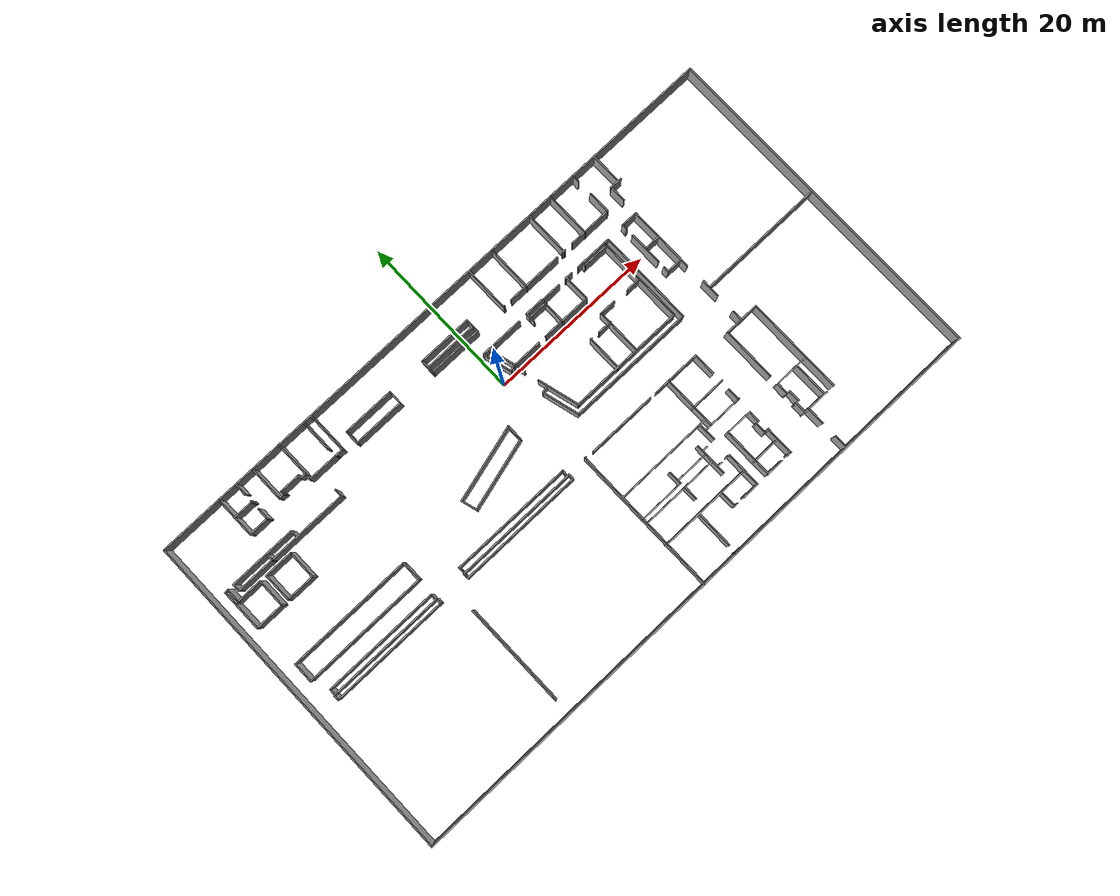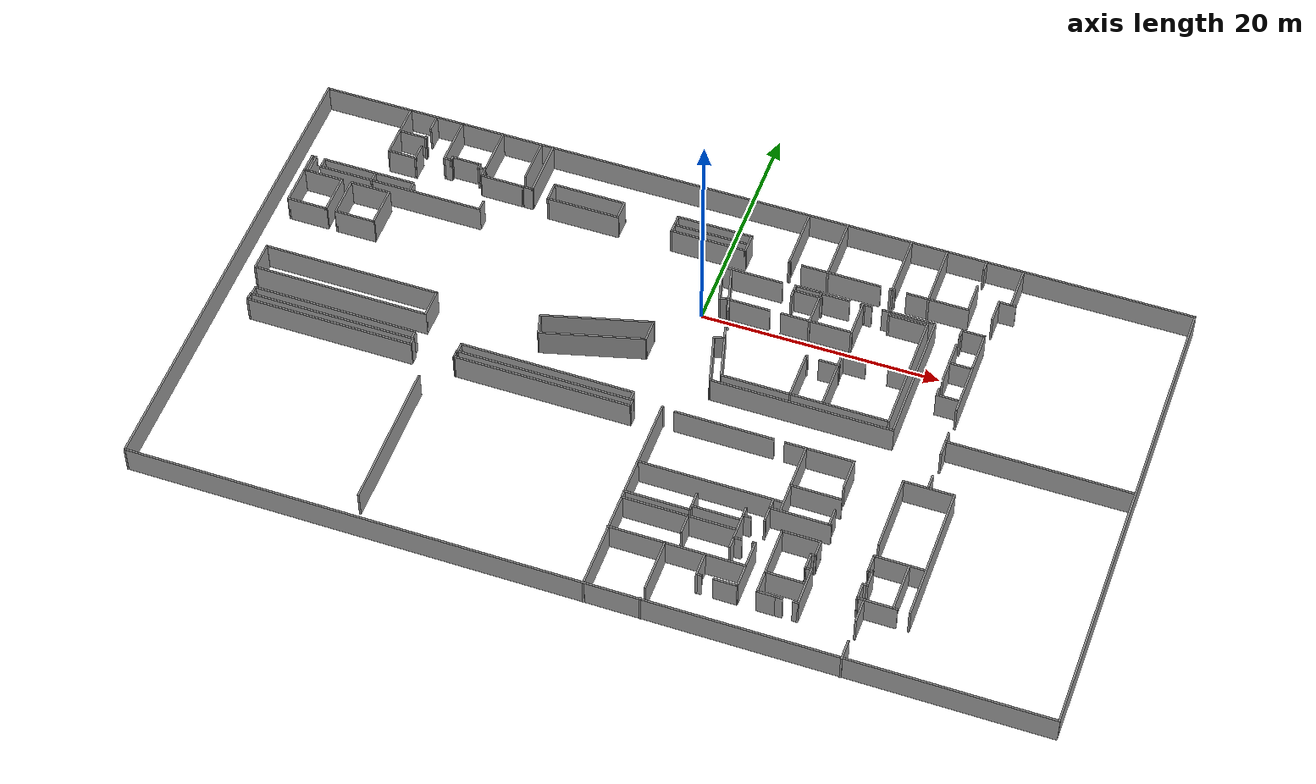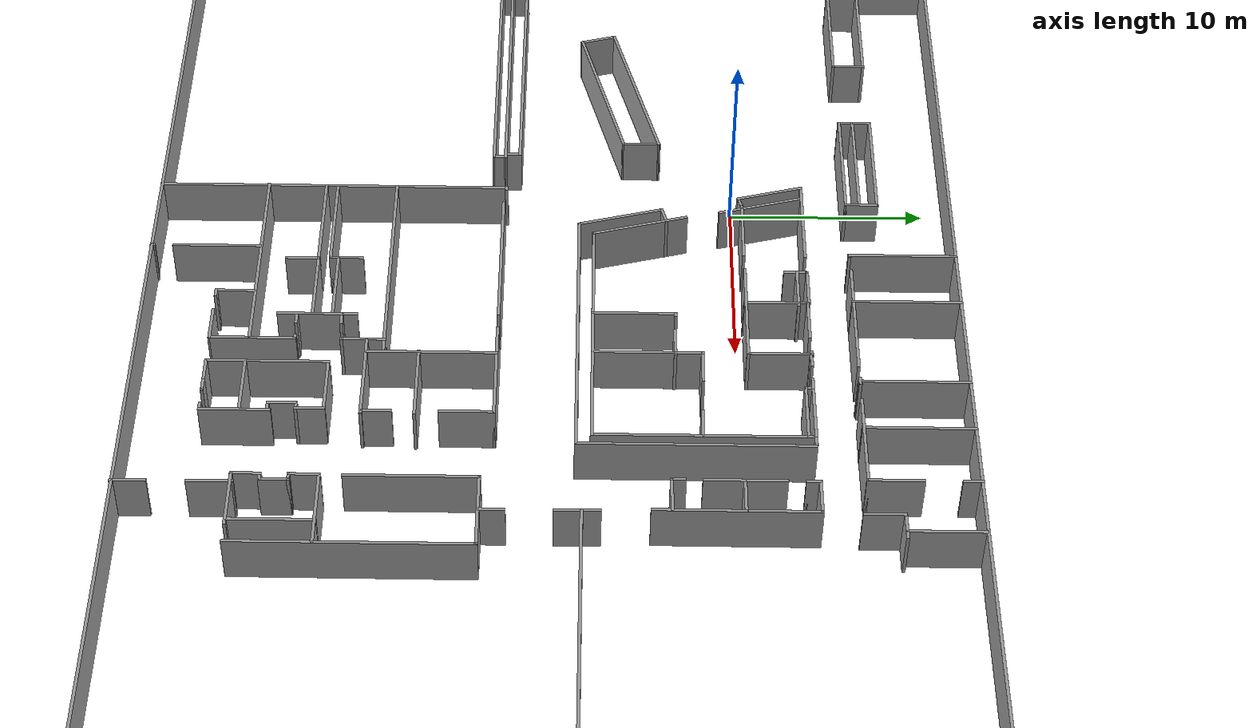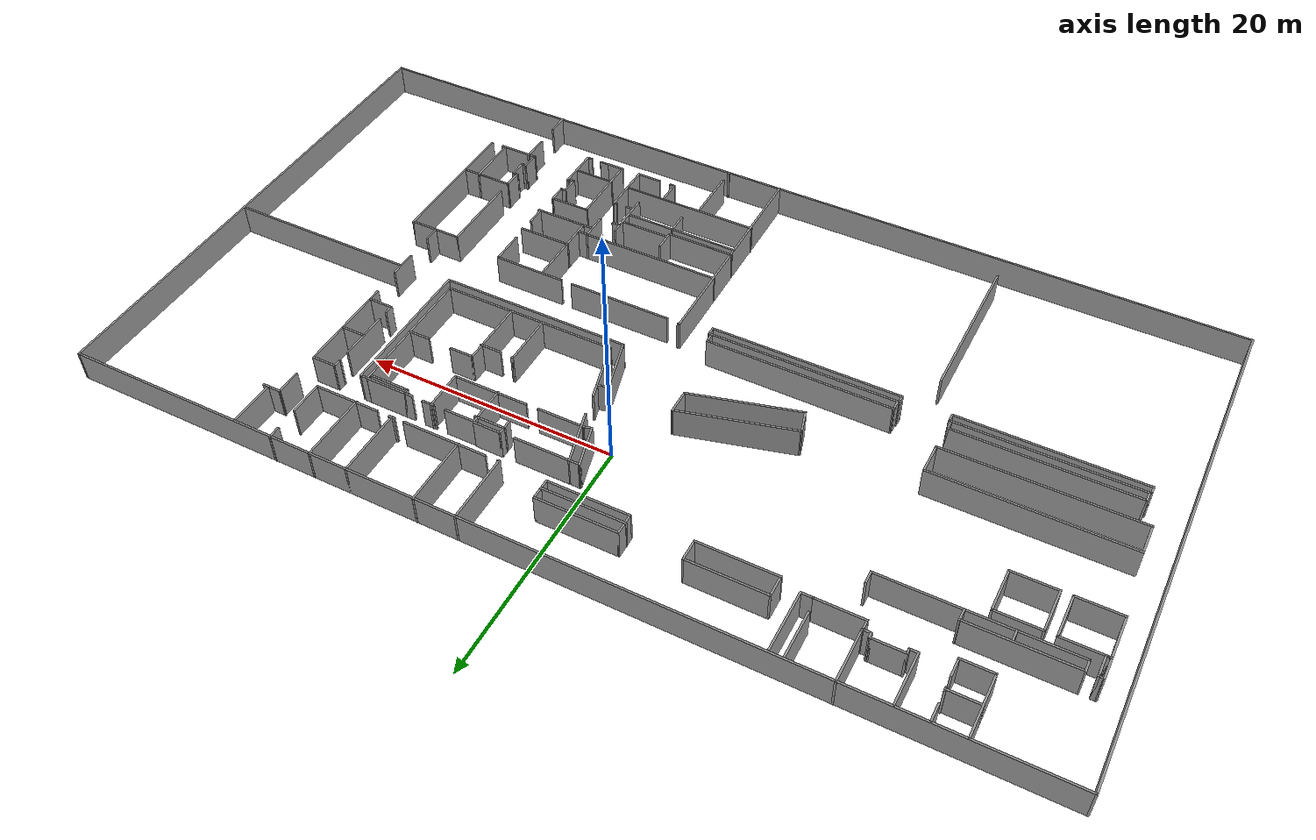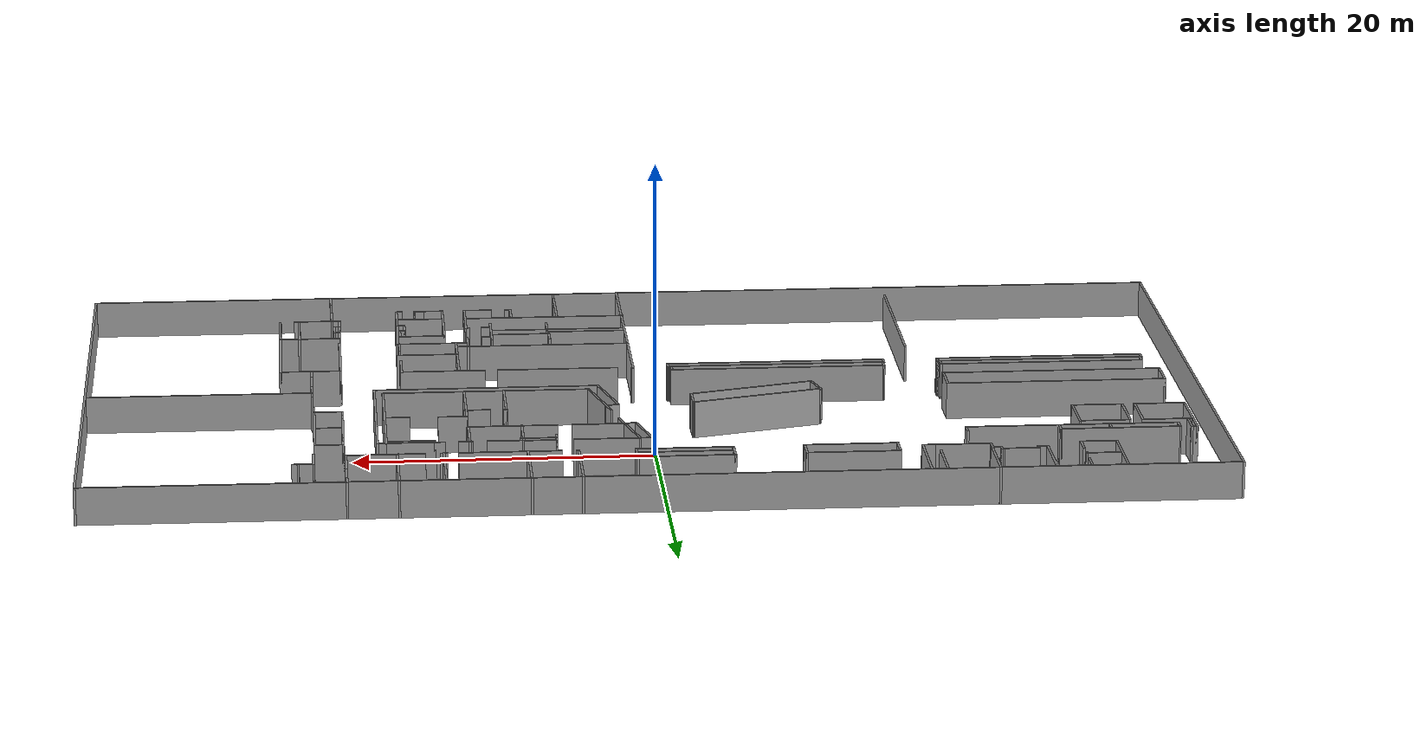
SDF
<?xml version='1.0'?>
<sdf version='1.7'>
  <model name='gix_2f'>
    <pose>0.287504 -9.19255 0 0 -0 0</pose>
    <link name='Wall_104'>
      <collision name='Wall_104_Collision'>
        <geometry>
          <box>
            <size>5.25 0.15 2.5</size>
          </box>
        </geometry>
        <pose>0 0 1.25 0 -0 0</pose>
      </collision>
      <visual name='Wall_104_Visual'>
        <pose>0 0 1.25 0 -0 0</pose>
        <geometry>
          <box>
            <size>5.25 0.15 2.5</size>
          </box>
        </geometry>
        <material>
          <script>
            <uri>file://media/materials/scripts/gazebo.material</uri>
            <name>Gazebo/Grey</name>
          </script>
          <ambient>1 1 1 1</ambient>
        </material>
        <meta>
          <layer>0</layer>
        </meta>
      </visual>
      <pose>17.6956 14.9975 0 0 -0 0</pose>
    </link>
    <link name='Wall_105'>
      <collision name='Wall_105_Collision'>
        <geometry>
          <box>
            <size>2.75 0.15 2.5</size>
          </box>
        </geometry>
        <pose>0 0 1.25 0 -0 0</pose>
      </collision>
      <visual name='Wall_105_Visual'>
        <pose>0 0 1.25 0 -0 0</pose>
        <geometry>
          <box>
            <size>2.75 0.15 2.5</size>
          </box>
        </geometry>
        <material>
          <script>
            <uri>file://media/materials/scripts/gazebo.material</uri>
            <name>Gazebo/Grey</name>
          </script>
          <ambient>1 1 1 1</ambient>
        </material>
        <meta>
          <layer>0</layer>
        </meta>
      </visual>
      <pose>20.2456 16.2975 0 0 -0 1.5708</pose>
    </link>
    <link name='Wall_107'>
      <collision name='Wall_107_Collision'>
        <geometry>
          <box>
            <size>1 0.15 2.5</size>
          </box>
        </geometry>
        <pose>0 0 1.25 0 -0 0</pose>
      </collision>
      <visual name='Wall_107_Visual'>
        <pose>0 0 1.25 0 -0 0</pose>
        <geometry>
          <box>
            <size>1 0.15 2.5</size>
          </box>
        </geometry>
        <material>
          <script>
            <uri>file://media/materials/scripts/gazebo.material</uri>
            <name>Gazebo/Grey</name>
          </script>
          <ambient>1 1 1 1</ambient>
        </material>
        <meta>
          <layer>0</layer>
        </meta>
      </visual>
      <pose>20.2383 19.9081 0 0 -0 -1.5708</pose>
    </link>
    <link name='Wall_109'>
      <collision name='Wall_109_Collision'>
        <geometry>
          <box>
            <size>5.5 0.15 2.5</size>
          </box>
        </geometry>
        <pose>0 0 1.25 0 -0 0</pose>
      </collision>
      <visual name='Wall_109_Visual'>
        <pose>0 0 1.25 0 -0 0</pose>
        <geometry>
          <box>
            <size>5.5 0.15 2.5</size>
          </box>
        </geometry>
        <material>
          <script>
            <uri>file://media/materials/scripts/gazebo.material</uri>
            <name>Gazebo/Grey</name>
          </script>
          <ambient>1 1 1 1</ambient>
        </material>
        <meta>
          <layer>0</layer>
        </meta>
      </visual>
      <pose>16.9145 17.64 0 0 -0 -1.5708</pose>
    </link>
    <link name='Wall_11'>
      <collision name='Wall_11_Collision'>
        <geometry>
          <box>
            <size>15 0.15 2.5</size>
          </box>
        </geometry>
        <pose>0 0 1.25 0 -0 0</pose>
      </collision>
      <visual name='Wall_11_Visual'>
        <pose>0 0 1.25 0 -0 0</pose>
        <geometry>
          <box>
            <size>15 0.15 2.5</size>
          </box>
        </geometry>
        <material>
          <script>
            <uri>file://media/materials/scripts/gazebo.material</uri>
            <name>Gazebo/Grey</name>
          </script>
          <ambient>1 1 1 1</ambient>
        </material>
        <meta>
          <layer>0</layer>
        </meta>
      </visual>
      <pose>-9.43001 -2.59263 0 0 -0 0</pose>
    </link>
    <link name='Wall_113'>
      <collision name='Wall_113_Collision'>
        <geometry>
          <box>
            <size>3.75 0.15 2.5</size>
          </box>
        </geometry>
        <pose>0 0 1.25 0 -0 0</pose>
      </collision>
      <visual name='Wall_113_Visual'>
        <pose>0 0 1.25 0 -0 0</pose>
        <geometry>
          <box>
            <size>3.75 0.15 2.5</size>
          </box>
        </geometry>
        <material>
          <script>
            <uri>file://media/materials/scripts/gazebo.material</uri>
            <name>Gazebo/Grey</name>
          </script>
          <ambient>1 1 1 1</ambient>
        </material>
        <meta>
          <layer>0</layer>
        </meta>
      </visual>
      <pose>23.3339 18.431 0 0 -0 1.5708</pose>
    </link>
    <link name='Wall_116'>
      <collision name='Wall_116_Collision'>
        <geometry>
          <box>
            <size>1.5 0.15 2.5</size>
          </box>
        </geometry>
        <pose>0 0 1.25 0 -0 0</pose>
      </collision>
      <visual name='Wall_116_Visual'>
        <pose>0 0 1.25 0 -0 0</pose>
        <geometry>
          <box>
            <size>1.5 0.15 2.5</size>
          </box>
        </geometry>
        <material>
          <script>
            <uri>file://media/materials/scripts/gazebo.material</uri>
            <name>Gazebo/Grey</name>
          </script>
          <ambient>1 1 1 1</ambient>
        </material>
        <meta>
          <layer>0</layer>
        </meta>
      </visual>
      <pose>23.0121 16.5984 0 0 -0 0</pose>
    </link>
    <link name='Wall_118'>
      <collision name='Wall_118_Collision'>
        <geometry>
          <box>
            <size>2.0449 0.15 2.5</size>
          </box>
        </geometry>
        <pose>0 0 1.25 0 -0 0</pose>
      </collision>
      <visual name='Wall_118_Visual'>
        <pose>0 0 1.25 0 -0 0</pose>
        <geometry>
          <box>
            <size>2.0449 0.15 2.5</size>
          </box>
        </geometry>
        <material>
          <script>
            <uri>file://media/materials/scripts/gazebo.material</uri>
            <name>Gazebo/Grey</name>
          </script>
          <ambient>1 1 1 1</ambient>
        </material>
        <meta>
          <layer>0</layer>
        </meta>
      </visual>
      <pose>22.3357 15.651 0 0 -0 1.5693</pose>
    </link>
    <link name='Wall_12'>
      <collision name='Wall_12_Collision'>
        <geometry>
          <box>
            <size>0.747125 0.15 2.5</size>
          </box>
        </geometry>
        <pose>0 0 1.25 0 -0 0</pose>
      </collision>
      <visual name='Wall_12_Visual'>
        <pose>0 0 1.25 0 -0 0</pose>
        <geometry>
          <box>
            <size>0.747125 0.15 2.5</size>
          </box>
        </geometry>
        <material>
          <script>
            <uri>file://media/materials/scripts/gazebo.material</uri>
            <name>Gazebo/Grey</name>
          </script>
          <ambient>1 1 1 1</ambient>
        </material>
        <meta>
          <layer>0</layer>
        </meta>
      </visual>
      <pose>-2.00806 -2.89118 0 0 -0 -1.58103</pose>
    </link>
    <link name='Wall_120'>
      <collision name='Wall_120_Collision'>
        <geometry>
          <box>
            <size>0.16 0.15 2.5</size>
          </box>
        </geometry>
        <pose>0 0 1.25 0 -0 0</pose>
      </collision>
      <visual name='Wall_120_Visual'>
        <pose>0 0 1.25 0 -0 0</pose>
        <geometry>
          <box>
            <size>0.16 0.15 2.5</size>
          </box>
        </geometry>
        <material>
          <script>
            <uri>file://media/materials/scripts/gazebo.material</uri>
            <name>Gazebo/Grey</name>
          </script>
          <ambient>1 1 1 1</ambient>
        </material>
        <meta>
          <layer>0</layer>
        </meta>
      </visual>
      <pose>20.3829 12.1748 0 0 -0 0</pose>
    </link>
    <link name='Wall_121'>
      <collision name='Wall_121_Collision'>
        <geometry>
          <box>
            <size>0.75 0.15 2.5</size>
          </box>
        </geometry>
        <pose>0 0 1.25 0 -0 0</pose>
      </collision>
      <visual name='Wall_121_Visual'>
        <pose>0 0 1.25 0 -0 0</pose>
        <geometry>
          <box>
            <size>0.75 0.15 2.5</size>
          </box>
        </geometry>
        <material>
          <script>
            <uri>file://media/materials/scripts/gazebo.material</uri>
            <name>Gazebo/Grey</name>
          </script>
          <ambient>1 1 1 1</ambient>
        </material>
        <meta>
          <layer>0</layer>
        </meta>
      </visual>
      <pose>20.3879 12.4748 0 0 -0 1.5708</pose>
    </link>
    <link name='Wall_122'>
      <collision name='Wall_122_Collision'>
        <geometry>
          <box>
            <size>2 0.15 2.5</size>
          </box>
        </geometry>
        <pose>0 0 1.25 0 -0 0</pose>
      </collision>
      <visual name='Wall_122_Visual'>
        <pose>0 0 1.25 0 -0 0</pose>
        <geometry>
          <box>
            <size>2 0.15 2.5</size>
          </box>
        </geometry>
        <material>
          <script>
            <uri>file://media/materials/scripts/gazebo.material</uri>
            <name>Gazebo/Grey</name>
          </script>
          <ambient>1 1 1 1</ambient>
        </material>
        <meta>
          <layer>0</layer>
        </meta>
      </visual>
      <pose>21.3129 12.7748 0 0 -0 0</pose>
    </link>
    <link name='Wall_123'>
      <collision name='Wall_123_Collision'>
        <geometry>
          <box>
            <size>8 0.15 2.5</size>
          </box>
        </geometry>
        <pose>0 0 1.25 0 -0 0</pose>
      </collision>
      <visual name='Wall_123_Visual'>
        <pose>0 0 1.25 0 -0 0</pose>
        <geometry>
          <box>
            <size>8 0.15 2.5</size>
          </box>
        </geometry>
        <material>
          <script>
            <uri>file://media/materials/scripts/gazebo.material</uri>
            <name>Gazebo/Grey</name>
          </script>
          <ambient>1 1 1 1</ambient>
        </material>
        <meta>
          <layer>0</layer>
        </meta>
      </visual>
      <pose>22.2379 8.84977 0 0 -0 -1.5708</pose>
    </link>
    <link name='Wall_125'>
      <collision name='Wall_125_Collision'>
        <geometry>
          <box>
            <size>4 0.15 2.5</size>
          </box>
        </geometry>
        <pose>0 0 1.25 0 -0 0</pose>
      </collision>
      <visual name='Wall_125_Visual'>
        <pose>0 0 1.25 0 -0 0</pose>
        <geometry>
          <box>
            <size>4 0.15 2.5</size>
          </box>
        </geometry>
        <material>
          <script>
            <uri>file://media/materials/scripts/gazebo.material</uri>
            <name>Gazebo/Grey</name>
          </script>
          <ambient>1 1 1 1</ambient>
        </material>
        <meta>
          <layer>0</layer>
        </meta>
      </visual>
      <pose>20.3613 9.28577 0 0 -0 -1.5708</pose>
    </link>
    <link name='Wall_127'>
      <collision name='Wall_127_Collision'>
        <geometry>
          <box>
            <size>0.75 0.15 2.5</size>
          </box>
        </geometry>
        <pose>0 0 1.25 0 -0 0</pose>
      </collision>
      <visual name='Wall_127_Visual'>
        <pose>0 0 1.25 0 -0 0</pose>
        <geometry>
          <box>
            <size>0.75 0.15 2.5</size>
          </box>
        </geometry>
        <material>
          <script>
            <uri>file://media/materials/scripts/gazebo.material</uri>
            <name>Gazebo/Grey</name>
          </script>
          <ambient>1 1 1 1</ambient>
        </material>
        <meta>
          <layer>0</layer>
        </meta>
      </visual>
      <pose>20.3565 6.14583 0 0 -0 -1.5708</pose>
    </link>
    <link name='Wall_128'>
      <collision name='Wall_128_Collision'>
        <geometry>
          <box>
            <size>2 0.15 2.5</size>
          </box>
        </geometry>
        <pose>0 0 1.25 0 -0 0</pose>
      </collision>
      <visual name='Wall_128_Visual'>
        <pose>0 0 1.25 0 -0 0</pose>
        <geometry>
          <box>
            <size>2 0.15 2.5</size>
          </box>
        </geometry>
        <material>
          <script>
            <uri>file://media/materials/scripts/gazebo.material</uri>
            <name>Gazebo/Grey</name>
          </script>
          <ambient>1 1 1 1</ambient>
        </material>
        <meta>
          <layer>0</layer>
        </meta>
      </visual>
      <pose>21.2815 5.84583 0 0 -0 0</pose>
    </link>
    <link name='Wall_13'>
      <collision name='Wall_13_Collision'>
        <geometry>
          <box>
            <size>15 0.15 2.5</size>
          </box>
        </geometry>
        <pose>0 0 1.25 0 -0 0</pose>
      </collision>
      <visual name='Wall_13_Visual'>
        <pose>0 0 1.25 0 -0 0</pose>
        <geometry>
          <box>
            <size>15 0.15 2.5</size>
          </box>
        </geometry>
        <material>
          <script>
            <uri>file://media/materials/scripts/gazebo.material</uri>
            <name>Gazebo/Grey</name>
          </script>
          <ambient>1 1 1 1</ambient>
        </material>
        <meta>
          <layer>0</layer>
        </meta>
      </visual>
      <pose>-9.43612 -3.18973 0 0 -0 3.14159</pose>
    </link>
    <link name='Wall_130'>
      <collision name='Wall_130_Collision'>
        <geometry>
          <box>
            <size>2 0.15 2.5</size>
          </box>
        </geometry>
        <pose>0 0 1.25 0 -0 0</pose>
      </collision>
      <visual name='Wall_130_Visual'>
        <pose>0 0 1.25 0 -0 0</pose>
        <geometry>
          <box>
            <size>2 0.15 2.5</size>
          </box>
        </geometry>
        <material>
          <script>
            <uri>file://media/materials/scripts/gazebo.material</uri>
            <name>Gazebo/Grey</name>
          </script>
          <ambient>1 1 1 1</ambient>
        </material>
        <meta>
          <layer>0</layer>
        </meta>
      </visual>
      <pose>21.2959 9.26453 0 0 -0 0</pose>
    </link>
    <link name='Wall_132'>
      <collision name='Wall_132_Collision'>
        <geometry>
          <box>
            <size>2.25 0.15 2.5</size>
          </box>
        </geometry>
        <pose>0 0 1.25 0 -0 0</pose>
      </collision>
      <visual name='Wall_132_Visual'>
        <pose>0 0 1.25 0 -0 0</pose>
        <geometry>
          <box>
            <size>2.25 0.15 2.5</size>
          </box>
        </geometry>
        <material>
          <script>
            <uri>file://media/materials/scripts/gazebo.material</uri>
            <name>Gazebo/Grey</name>
          </script>
          <ambient>1 1 1 1</ambient>
        </material>
        <meta>
          <layer>0</layer>
        </meta>
      </visual>
      <pose>22.3373 1.44229 0 0 -0 -1.5708</pose>
    </link>
    <link name='Wall_134'>
      <collision name='Wall_134_Collision'>
        <geometry>
          <box>
            <size>15.25 0.15 2.5</size>
          </box>
        </geometry>
        <pose>0 0 1.25 0 -0 0</pose>
      </collision>
      <visual name='Wall_134_Visual'>
        <pose>0 0 1.25 0 -0 0</pose>
        <geometry>
          <box>
            <size>15.25 0.15 2.5</size>
          </box>
        </geometry>
        <material>
          <script>
            <uri>file://media/materials/scripts/gazebo.material</uri>
            <name>Gazebo/Grey</name>
          </script>
          <ambient>1 1 1 1</ambient>
        </material>
        <meta>
          <layer>0</layer>
        </meta>
      </visual>
      <pose>29.9039 1.64609 0 0 -0 0</pose>
    </link>
    <link name='Wall_136'>
      <collision name='Wall_136_Collision'>
        <geometry>
          <box>
            <size>6.5 0.15 2.5</size>
          </box>
        </geometry>
        <pose>0 0 1.25 0 -0 0</pose>
      </collision>
      <visual name='Wall_136_Visual'>
        <pose>0 0 1.25 0 -0 0</pose>
        <geometry>
          <box>
            <size>6.5 0.15 2.5</size>
          </box>
        </geometry>
        <material>
          <script>
            <uri>file://media/materials/scripts/gazebo.material</uri>
            <name>Gazebo/Grey</name>
          </script>
          <ambient>1 1 1 1</ambient>
        </material>
        <meta>
          <layer>0</layer>
        </meta>
      </visual>
      <pose>20.356 -6.31962 0 0 -0 1.5708</pose>
    </link>
    <link name='Wall_137'>
      <collision name='Wall_137_Collision'>
        <geometry>
          <box>
            <size>4.25 0.15 2.5</size>
          </box>
        </geometry>
        <pose>0 0 1.25 0 -0 0</pose>
      </collision>
      <visual name='Wall_137_Visual'>
        <pose>0 0 1.25 0 -0 0</pose>
        <geometry>
          <box>
            <size>4.25 0.15 2.5</size>
          </box>
        </geometry>
        <material>
          <script>
            <uri>file://media/materials/scripts/gazebo.material</uri>
            <name>Gazebo/Grey</name>
          </script>
          <ambient>1 1 1 1</ambient>
        </material>
        <meta>
          <layer>0</layer>
        </meta>
      </visual>
      <pose>22.406 -3.14462 0 0 -0 0</pose>
    </link>
    <link name='Wall_138'>
      <collision name='Wall_138_Collision'>
        <geometry>
          <box>
            <size>11.75 0.15 2.5</size>
          </box>
        </geometry>
        <pose>0 0 1.25 0 -0 0</pose>
      </collision>
      <visual name='Wall_138_Visual'>
        <pose>0 0 1.25 0 -0 0</pose>
        <geometry>
          <box>
            <size>11.75 0.15 2.5</size>
          </box>
        </geometry>
        <material>
          <script>
            <uri>file://media/materials/scripts/gazebo.material</uri>
            <name>Gazebo/Grey</name>
          </script>
          <ambient>1 1 1 1</ambient>
        </material>
        <meta>
          <layer>0</layer>
        </meta>
      </visual>
      <pose>24.456 -8.94462 0 0 -0 -1.5708</pose>
    </link>
    <link name='Wall_14'>
      <collision name='Wall_14_Collision'>
        <geometry>
          <box>
            <size>0.747125 0.15 2.5</size>
          </box>
        </geometry>
        <pose>0 0 1.25 0 -0 0</pose>
      </collision>
      <visual name='Wall_14_Visual'>
        <pose>0 0 1.25 0 -0 0</pose>
        <geometry>
          <box>
            <size>0.747125 0.15 2.5</size>
          </box>
        </geometry>
        <material>
          <script>
            <uri>file://media/materials/scripts/gazebo.material</uri>
            <name>Gazebo/Grey</name>
          </script>
          <ambient>1 1 1 1</ambient>
        </material>
        <meta>
          <layer>0</layer>
        </meta>
      </visual>
      <pose>-16.8581 -2.89118 0 0 -0 1.56056</pose>
    </link>
    <link name='Wall_140'>
      <collision name='Wall_140_Collision'>
        <geometry>
          <box>
            <size>1.25 0.15 2.5</size>
          </box>
        </geometry>
        <pose>0 0 1.25 0 -0 0</pose>
      </collision>
      <visual name='Wall_140_Visual'>
        <pose>0 0 1.25 0 -0 0</pose>
        <geometry>
          <box>
            <size>1.25 0.15 2.5</size>
          </box>
        </geometry>
        <material>
          <script>
            <uri>file://media/materials/scripts/gazebo.material</uri>
            <name>Gazebo/Grey</name>
          </script>
          <ambient>1 1 1 1</ambient>
        </material>
        <meta>
          <layer>0</layer>
        </meta>
      </visual>
      <pose>22.3435 -2.49513 0 0 -0 -1.5708</pose>
    </link>
    <link name='Wall_142'>
      <collision name='Wall_142_Collision'>
        <geometry>
          <box>
            <size>4.25 0.15 2.5</size>
          </box>
        </geometry>
        <pose>0 0 1.25 0 -0 0</pose>
      </collision>
      <visual name='Wall_142_Visual'>
        <pose>0 0 1.25 0 -0 0</pose>
        <geometry>
          <box>
            <size>4.25 0.15 2.5</size>
          </box>
        </geometry>
        <material>
          <script>
            <uri>file://media/materials/scripts/gazebo.material</uri>
            <name>Gazebo/Grey</name>
          </script>
          <ambient>1 1 1 1</ambient>
        </material>
        <meta>
          <layer>0</layer>
        </meta>
      </visual>
      <pose>22.396 -10.6333 0 0 -0 0</pose>
    </link>
    <link name='Wall_144'>
      <collision name='Wall_144_Collision'>
        <geometry>
          <box>
            <size>3.25 0.15 2.5</size>
          </box>
        </geometry>
        <pose>0 0 1.25 0 -0 0</pose>
      </collision>
      <visual name='Wall_144_Visual'>
        <pose>0 0 1.25 0 -0 0</pose>
        <geometry>
          <box>
            <size>3.25 0.15 2.5</size>
          </box>
        </geometry>
        <material>
          <script>
            <uri>file://media/materials/scripts/gazebo.material</uri>
            <name>Gazebo/Grey</name>
          </script>
          <ambient>1 1 1 1</ambient>
        </material>
        <meta>
          <layer>0</layer>
        </meta>
      </visual>
      <pose>21.8553 -14.7544 0 0 -0 3.14159</pose>
    </link>
    <link name='Wall_145'>
      <collision name='Wall_145_Collision'>
        <geometry>
          <box>
            <size>0.16 0.15 2.5</size>
          </box>
        </geometry>
        <pose>0 0 1.25 0 -0 0</pose>
      </collision>
      <visual name='Wall_145_Visual'>
        <pose>0 0 1.25 0 -0 0</pose>
        <geometry>
          <box>
            <size>0.16 0.15 2.5</size>
          </box>
        </geometry>
        <material>
          <script>
            <uri>file://media/materials/scripts/gazebo.material</uri>
            <name>Gazebo/Grey</name>
          </script>
          <ambient>1 1 1 1</ambient>
        </material>
        <meta>
          <layer>0</layer>
        </meta>
      </visual>
      <pose>20.3103 -14.7544 0 0 -0 0</pose>
    </link>
    <link name='Wall_146'>
      <collision name='Wall_146_Collision'>
        <geometry>
          <box>
            <size>1.5 0.15 2.5</size>
          </box>
        </geometry>
        <pose>0 0 1.25 0 -0 0</pose>
      </collision>
      <visual name='Wall_146_Visual'>
        <pose>0 0 1.25 0 -0 0</pose>
        <geometry>
          <box>
            <size>1.5 0.15 2.5</size>
          </box>
        </geometry>
        <material>
          <script>
            <uri>file://media/materials/scripts/gazebo.material</uri>
            <name>Gazebo/Grey</name>
          </script>
          <ambient>1 1 1 1</ambient>
        </material>
        <meta>
          <layer>0</layer>
        </meta>
      </visual>
      <pose>20.3153 -14.0794 0 0 -0 1.5708</pose>
    </link>
    <link name='Wall_147'>
      <collision name='Wall_147_Collision'>
        <geometry>
          <box>
            <size>0.5 0.15 2.5</size>
          </box>
        </geometry>
        <pose>0 0 1.25 0 -0 0</pose>
      </collision>
      <visual name='Wall_147_Visual'>
        <pose>0 0 1.25 0 -0 0</pose>
        <geometry>
          <box>
            <size>0.5 0.15 2.5</size>
          </box>
        </geometry>
        <material>
          <script>
            <uri>file://media/materials/scripts/gazebo.material</uri>
            <name>Gazebo/Grey</name>
          </script>
          <ambient>1 1 1 1</ambient>
        </material>
        <meta>
          <layer>0</layer>
        </meta>
      </visual>
      <pose>20.4903 -13.4044 0 0 -0 0</pose>
    </link>
    <link name='Wall_148'>
      <collision name='Wall_148_Collision'>
        <geometry>
          <box>
            <size>0.16 0.15 2.5</size>
          </box>
        </geometry>
        <pose>0 0 1.25 0 -0 0</pose>
      </collision>
      <visual name='Wall_148_Visual'>
        <pose>0 0 1.25 0 -0 0</pose>
        <geometry>
          <box>
            <size>0.16 0.15 2.5</size>
          </box>
        </geometry>
        <material>
          <script>
            <uri>file://media/materials/scripts/gazebo.material</uri>
            <name>Gazebo/Grey</name>
          </script>
          <ambient>1 1 1 1</ambient>
        </material>
        <meta>
          <layer>0</layer>
        </meta>
      </visual>
      <pose>20.6703 -13.4044 0 0 -0 0</pose>
    </link>
    <link name='Wall_149'>
      <collision name='Wall_149_Collision'>
        <geometry>
          <box>
            <size>1.5 0.15 2.5</size>
          </box>
        </geometry>
        <pose>0 0 1.25 0 -0 0</pose>
      </collision>
      <visual name='Wall_149_Visual'>
        <pose>0 0 1.25 0 -0 0</pose>
        <geometry>
          <box>
            <size>1.5 0.15 2.5</size>
          </box>
        </geometry>
        <material>
          <script>
            <uri>file://media/materials/scripts/gazebo.material</uri>
            <name>Gazebo/Grey</name>
          </script>
          <ambient>1 1 1 1</ambient>
        </material>
        <meta>
          <layer>0</layer>
        </meta>
      </visual>
      <pose>20.6753 -12.7294 0 0 -0 1.5708</pose>
    </link>
    <link name='Wall_150'>
      <collision name='Wall_150_Collision'>
        <geometry>
          <box>
            <size>0.5 0.15 2.5</size>
          </box>
        </geometry>
        <pose>0 0 1.25 0 -0 0</pose>
      </collision>
      <visual name='Wall_150_Visual'>
        <pose>0 0 1.25 0 -0 0</pose>
        <geometry>
          <box>
            <size>0.5 0.15 2.5</size>
          </box>
        </geometry>
        <material>
          <script>
            <uri>file://media/materials/scripts/gazebo.material</uri>
            <name>Gazebo/Grey</name>
          </script>
          <ambient>1 1 1 1</ambient>
        </material>
        <meta>
          <layer>0</layer>
        </meta>
      </visual>
      <pose>20.5003 -12.0544 0 0 -0 3.14159</pose>
    </link>
    <link name='Wall_151'>
      <collision name='Wall_151_Collision'>
        <geometry>
          <box>
            <size>1.57121 0.15 2.5</size>
          </box>
        </geometry>
        <pose>0 0 1.25 0 -0 0</pose>
      </collision>
      <visual name='Wall_151_Visual'>
        <pose>0 0 1.25 0 -0 0</pose>
        <geometry>
          <box>
            <size>1.57121 0.15 2.5</size>
          </box>
        </geometry>
        <material>
          <script>
            <uri>file://media/materials/scripts/gazebo.material</uri>
            <name>Gazebo/Grey</name>
          </script>
          <ambient>1 1 1 1</ambient>
        </material>
        <meta>
          <layer>0</layer>
        </meta>
      </visual>
      <pose>20.3357 -11.3438 0 0 -0 1.55622</pose>
    </link>
    <link name='Wall_154'>
      <collision name='Wall_154_Collision'>
        <geometry>
          <box>
            <size>4.25 0.15 2.5</size>
          </box>
        </geometry>
        <pose>0 0 1.25 0 -0 0</pose>
      </collision>
      <visual name='Wall_154_Visual'>
        <pose>0 0 1.25 0 -0 0</pose>
        <geometry>
          <box>
            <size>4.25 0.15 2.5</size>
          </box>
        </geometry>
        <material>
          <script>
            <uri>file://media/materials/scripts/gazebo.material</uri>
            <name>Gazebo/Grey</name>
          </script>
          <ambient>1 1 1 1</ambient>
        </material>
        <meta>
          <layer>0</layer>
        </meta>
      </visual>
      <pose>23.129 -12.6736 0 0 -0 -1.5708</pose>
    </link>
    <link name='Wall_156'>
      <collision name='Wall_156_Collision'>
        <geometry>
          <box>
            <size>2.25 0.15 2.5</size>
          </box>
        </geometry>
        <pose>0 0 1.25 0 -0 0</pose>
      </collision>
      <visual name='Wall_156_Visual'>
        <pose>0 0 1.25 0 -0 0</pose>
        <geometry>
          <box>
            <size>2.25 0.15 2.5</size>
          </box>
        </geometry>
        <material>
          <script>
            <uri>file://media/materials/scripts/gazebo.material</uri>
            <name>Gazebo/Grey</name>
          </script>
          <ambient>1 1 1 1</ambient>
        </material>
        <meta>
          <layer>0</layer>
        </meta>
      </visual>
      <pose>20.826 -15.7164 0 0 -0 1.5708</pose>
    </link>
    <link name='Wall_158'>
      <collision name='Wall_158_Collision'>
        <geometry>
          <box>
            <size>1.75 0.15 2.5</size>
          </box>
        </geometry>
        <pose>0 0 1.25 0 -0 0</pose>
      </collision>
      <visual name='Wall_158_Visual'>
        <pose>0 0 1.25 0 -0 0</pose>
        <geometry>
          <box>
            <size>1.75 0.15 2.5</size>
          </box>
        </geometry>
        <material>
          <script>
            <uri>file://media/materials/scripts/gazebo.material</uri>
            <name>Gazebo/Grey</name>
          </script>
          <ambient>1 1 1 1</ambient>
        </material>
        <meta>
          <layer>0</layer>
        </meta>
      </visual>
      <pose>20.8495 -19.5331 0 0 -0 -1.5708</pose>
    </link>
    <link name='Wall_16'>
      <collision name='Wall_16_Collision'>
        <geometry>
          <box>
            <size>40.75 0.15 2.5</size>
          </box>
        </geometry>
        <pose>0 0 1.25 0 -0 0</pose>
      </collision>
      <visual name='Wall_16_Visual'>
        <pose>0 0 1.25 0 -0 0</pose>
        <geometry>
          <box>
            <size>40.75 0.15 2.5</size>
          </box>
        </geometry>
        <material>
          <script>
            <uri>file://media/materials/scripts/gazebo.material</uri>
            <name>Gazebo/Grey</name>
          </script>
          <ambient>1 1 1 1</ambient>
        </material>
        <meta>
          <layer>0</layer>
        </meta>
      </visual>
      <pose>-37.55 0.010736 0 0 -0 1.5708</pose>
    </link>
    <link name='Wall_160'>
      <collision name='Wall_160_Collision'>
        <geometry>
          <box>
            <size>18 0.15 2.5</size>
          </box>
        </geometry>
        <pose>0 0 1.25 0 -0 0</pose>
      </collision>
      <visual name='Wall_160_Visual'>
        <pose>0 0 1.25 0 -0 0</pose>
        <geometry>
          <box>
            <size>18 0.15 2.5</size>
          </box>
        </geometry>
        <material>
          <script>
            <uri>file://media/materials/scripts/gazebo.material</uri>
            <name>Gazebo/Grey</name>
          </script>
          <ambient>1 1 1 1</ambient>
        </material>
        <meta>
          <layer>0</layer>
        </meta>
      </visual>
      <pose>0.398763 -11.388 0 0 -0 1.5708</pose>
    </link>
    <link name='Wall_161'>
      <collision name='Wall_161_Collision'>
        <geometry>
          <box>
            <size>0.25 0.15 2.5</size>
          </box>
        </geometry>
        <pose>0 0 1.25 0 -0 0</pose>
      </collision>
      <visual name='Wall_161_Visual'>
        <pose>0 0 1.25 0 -0 0</pose>
        <geometry>
          <box>
            <size>0.25 0.15 2.5</size>
          </box>
        </geometry>
        <material>
          <script>
            <uri>file://media/materials/scripts/gazebo.material</uri>
            <name>Gazebo/Grey</name>
          </script>
          <ambient>1 1 1 1</ambient>
        </material>
        <meta>
          <layer>0</layer>
        </meta>
      </visual>
      <pose>0.448763 -2.46302 0 0 -0 0</pose>
    </link>
    <link name='Wall_164'>
      <collision name='Wall_164_Collision'>
        <geometry>
          <box>
            <size>8.25 0.15 2.5</size>
          </box>
        </geometry>
        <pose>0 0 1.25 0 -0 0</pose>
      </collision>
      <visual name='Wall_164_Visual'>
        <pose>0 0 1.25 0 -0 0</pose>
        <geometry>
          <box>
            <size>8.25 0.15 2.5</size>
          </box>
        </geometry>
        <material>
          <script>
            <uri>file://media/materials/scripts/gazebo.material</uri>
            <name>Gazebo/Grey</name>
          </script>
          <ambient>1 1 1 1</ambient>
        </material>
        <meta>
          <layer>0</layer>
        </meta>
      </visual>
      <pose>5.57058 -2.58584 0 0 -0 0</pose>
    </link>
    <link name='Wall_168'>
      <collision name='Wall_168_Collision'>
        <geometry>
          <box>
            <size>5.75 0.15 2.5</size>
          </box>
        </geometry>
        <pose>0 0 1.25 0 -0 0</pose>
      </collision>
      <visual name='Wall_168_Visual'>
        <pose>0 0 1.25 0 -0 0</pose>
        <geometry>
          <box>
            <size>5.75 0.15 2.5</size>
          </box>
        </geometry>
        <material>
          <script>
            <uri>file://media/materials/scripts/gazebo.material</uri>
            <name>Gazebo/Grey</name>
          </script>
          <ambient>1 1 1 1</ambient>
        </material>
        <meta>
          <layer>0</layer>
        </meta>
      </visual>
      <pose>13.4074 -2.59567 0 0 -0 0</pose>
    </link>
    <link name='Wall_169'>
      <collision name='Wall_169_Collision'>
        <geometry>
          <box>
            <size>2.75 0.15 2.5</size>
          </box>
        </geometry>
        <pose>0 0 1.25 0 -0 0</pose>
      </collision>
      <visual name='Wall_169_Visual'>
        <pose>0 0 1.25 0 -0 0</pose>
        <geometry>
          <box>
            <size>2.75 0.15 2.5</size>
          </box>
        </geometry>
        <material>
          <script>
            <uri>file://media/materials/scripts/gazebo.material</uri>
            <name>Gazebo/Grey</name>
          </script>
          <ambient>1 1 1 1</ambient>
        </material>
        <meta>
          <layer>0</layer>
        </meta>
      </visual>
      <pose>16.2074 -3.89568 0 0 -0 -1.5708</pose>
    </link>
    <link name='Wall_171'>
      <collision name='Wall_171_Collision'>
        <geometry>
          <box>
            <size>1.5 0.15 2.5</size>
          </box>
        </geometry>
        <pose>0 0 1.25 0 -0 0</pose>
      </collision>
      <visual name='Wall_171_Visual'>
        <pose>0 0 1.25 0 -0 0</pose>
        <geometry>
          <box>
            <size>1.5 0.15 2.5</size>
          </box>
        </geometry>
        <material>
          <script>
            <uri>file://media/materials/scripts/gazebo.material</uri>
            <name>Gazebo/Grey</name>
          </script>
          <ambient>1 1 1 1</ambient>
        </material>
        <meta>
          <layer>0</layer>
        </meta>
      </visual>
      <pose>16.2286 -8.22332 0 0 -0 -1.5708</pose>
    </link>
    <link name='Wall_174'>
      <collision name='Wall_174_Collision'>
        <geometry>
          <box>
            <size>6.5 0.15 2.5</size>
          </box>
        </geometry>
        <pose>0 0 1.25 0 -0 0</pose>
      </collision>
      <visual name='Wall_174_Visual'>
        <pose>0 0 1.25 0 -0 0</pose>
        <geometry>
          <box>
            <size>6.5 0.15 2.5</size>
          </box>
        </geometry>
        <material>
          <script>
            <uri>file://media/materials/scripts/gazebo.material</uri>
            <name>Gazebo/Grey</name>
          </script>
          <ambient>1 1 1 1</ambient>
        </material>
        <meta>
          <layer>0</layer>
        </meta>
      </visual>
      <pose>12.2884 -5.79752 0 0 -0 -1.5708</pose>
    </link>
    <link name='Wall_176'>
      <collision name='Wall_176_Collision'>
        <geometry>
          <box>
            <size>5 0.15 2.5</size>
          </box>
        </geometry>
        <pose>0 0 1.25 0 -0 0</pose>
      </collision>
      <visual name='Wall_176_Visual'>
        <pose>0 0 1.25 0 -0 0</pose>
        <geometry>
          <box>
            <size>5 0.15 2.5</size>
          </box>
        </geometry>
        <material>
          <script>
            <uri>file://media/materials/scripts/gazebo.material</uri>
            <name>Gazebo/Grey</name>
          </script>
          <ambient>1 1 1 1</ambient>
        </material>
        <meta>
          <layer>0</layer>
        </meta>
      </visual>
      <pose>13.9309 -8.97341 0 0 -0 0</pose>
    </link>
    <link name='Wall_178'>
      <collision name='Wall_178_Collision'>
        <geometry>
          <box>
            <size>4.25 0.15 2.5</size>
          </box>
        </geometry>
        <pose>0 0 1.25 0 -0 0</pose>
      </collision>
      <visual name='Wall_178_Visual'>
        <pose>0 0 1.25 0 -0 0</pose>
        <geometry>
          <box>
            <size>4.25 0.15 2.5</size>
          </box>
        </geometry>
        <material>
          <script>
            <uri>file://media/materials/scripts/gazebo.material</uri>
            <name>Gazebo/Grey</name>
          </script>
          <ambient>1 1 1 1</ambient>
        </material>
        <meta>
          <layer>0</layer>
        </meta>
      </visual>
      <pose>14.3197 -6.39481 0 0 -0 0</pose>
    </link>
    <link name='Wall_180'>
      <collision name='Wall_180_Collision'>
        <geometry>
          <box>
            <size>12 0.15 2.5</size>
          </box>
        </geometry>
        <pose>0 0 1.25 0 -0 0</pose>
      </collision>
      <visual name='Wall_180_Visual'>
        <pose>0 0 1.25 0 -0 0</pose>
        <geometry>
          <box>
            <size>12 0.15 2.5</size>
          </box>
        </geometry>
        <material>
          <script>
            <uri>file://media/materials/scripts/gazebo.material</uri>
            <name>Gazebo/Grey</name>
          </script>
          <ambient>1 1 1 1</ambient>
        </material>
        <meta>
          <layer>0</layer>
        </meta>
      </visual>
      <pose>6.32009 -8.12995 0 0 -0 0</pose>
    </link>
    <link name='Wall_182'>
      <collision name='Wall_182_Collision'>
        <geometry>
          <box>
            <size>2.25 0.15 2.5</size>
          </box>
        </geometry>
        <pose>0 0 1.25 0 -0 0</pose>
      </collision>
      <visual name='Wall_182_Visual'>
        <pose>0 0 1.25 0 -0 0</pose>
        <geometry>
          <box>
            <size>2.25 0.15 2.5</size>
          </box>
        </geometry>
        <material>
          <script>
            <uri>file://media/materials/scripts/gazebo.material</uri>
            <name>Gazebo/Grey</name>
          </script>
          <ambient>1 1 1 1</ambient>
        </material>
        <meta>
          <layer>0</layer>
        </meta>
      </visual>
      <pose>11.4573 -9.17497 0 0 -0 -1.5708</pose>
    </link>
    <link name='Wall_183'>
      <collision name='Wall_183_Collision'>
        <geometry>
          <box>
            <size>0.15 0.15 2.5</size>
          </box>
        </geometry>
        <pose>0 0 1.25 0 -0 0</pose>
      </collision>
      <visual name='Wall_183_Visual'>
        <pose>0 0 1.25 0 -0 0</pose>
        <geometry>
          <box>
            <size>0.15 0.15 2.5</size>
          </box>
        </geometry>
        <material>
          <script>
            <uri>file://media/materials/scripts/gazebo.material</uri>
            <name>Gazebo/Grey</name>
          </script>
          <ambient>1 1 1 1</ambient>
        </material>
        <meta>
          <layer>0</layer>
        </meta>
      </visual>
      <pose>11.4573 -10.225 0 0 -0 0</pose>
    </link>
    <link name='Wall_185'>
      <collision name='Wall_185_Collision'>
        <geometry>
          <box>
            <size>4 0.15 2.5</size>
          </box>
        </geometry>
        <pose>0 0 1.25 0 -0 0</pose>
      </collision>
      <visual name='Wall_185_Visual'>
        <pose>0 0 1.25 0 -0 0</pose>
        <geometry>
          <box>
            <size>4 0.15 2.5</size>
          </box>
        </geometry>
        <material>
          <script>
            <uri>file://media/materials/scripts/gazebo.material</uri>
            <name>Gazebo/Grey</name>
          </script>
          <ambient>1 1 1 1</ambient>
        </material>
        <meta>
          <layer>0</layer>
        </meta>
      </visual>
      <pose>9.73962 -11.5348 0 0 -0 -1.5708</pose>
    </link>
    <link name='Wall_187'>
      <collision name='Wall_187_Collision'>
        <geometry>
          <box>
            <size>0.75 0.15 2.5</size>
          </box>
        </geometry>
        <pose>0 0 1.25 0 -0 0</pose>
      </collision>
      <visual name='Wall_187_Visual'>
        <pose>0 0 1.25 0 -0 0</pose>
        <geometry>
          <box>
            <size>0.75 0.15 2.5</size>
          </box>
        </geometry>
        <material>
          <script>
            <uri>file://media/materials/scripts/gazebo.material</uri>
            <name>Gazebo/Grey</name>
          </script>
          <ambient>1 1 1 1</ambient>
        </material>
        <meta>
          <layer>0</layer>
        </meta>
      </visual>
      <pose>10.0453 -10.3188 0 0 -0 0</pose>
    </link>
    <link name='Wall_189'>
      <collision name='Wall_189_Collision'>
        <geometry>
          <box>
            <size>0.75 0.15 2.5</size>
          </box>
        </geometry>
        <pose>0 0 1.25 0 -0 0</pose>
      </collision>
      <visual name='Wall_189_Visual'>
        <pose>0 0 1.25 0 -0 0</pose>
        <geometry>
          <box>
            <size>0.75 0.15 2.5</size>
          </box>
        </geometry>
        <material>
          <script>
            <uri>file://media/materials/scripts/gazebo.material</uri>
            <name>Gazebo/Grey</name>
          </script>
          <ambient>1 1 1 1</ambient>
        </material>
        <meta>
          <layer>0</layer>
        </meta>
      </visual>
      <pose>10.0511 -12.5372 0 0 -0 0</pose>
    </link>
    <link name='Wall_19'>
      <collision name='Wall_19_Collision'>
        <geometry>
          <box>
            <size>75.25 0.15 2.5</size>
          </box>
        </geometry>
        <pose>0 0 1.25 0 -0 0</pose>
      </collision>
      <visual name='Wall_19_Visual'>
        <pose>0 0 1.25 0 -0 0</pose>
        <geometry>
          <box>
            <size>75.25 0.15 2.5</size>
          </box>
        </geometry>
        <material>
          <script>
            <uri>file://media/materials/scripts/gazebo.material</uri>
            <name>Gazebo/Grey</name>
          </script>
          <ambient>1 1 1 1</ambient>
        </material>
        <meta>
          <layer>0</layer>
        </meta>
      </visual>
      <pose>-0 20.3107 0 0 -0 0</pose>
    </link>
    <link name='Wall_191'>
      <collision name='Wall_191_Collision'>
        <geometry>
          <box>
            <size>0.25 0.15 2.5</size>
          </box>
        </geometry>
        <pose>0 0 1.25 0 -0 0</pose>
      </collision>
      <visual name='Wall_191_Visual'>
        <pose>0 0 1.25 0 -0 0</pose>
        <geometry>
          <box>
            <size>0.25 0.15 2.5</size>
          </box>
        </geometry>
        <material>
          <script>
            <uri>file://media/materials/scripts/gazebo.material</uri>
            <name>Gazebo/Grey</name>
          </script>
          <ambient>1 1 1 1</ambient>
        </material>
        <meta>
          <layer>0</layer>
        </meta>
      </visual>
      <pose>11.3391 -12.5143 0 0 -0 0</pose>
    </link>
    <link name='Wall_194'>
      <collision name='Wall_194_Collision'>
        <geometry>
          <box>
            <size>2 0.15 2.5</size>
          </box>
        </geometry>
        <pose>0 0 1.25 0 -0 0</pose>
      </collision>
      <visual name='Wall_194_Visual'>
        <pose>0 0 1.25 0 -0 0</pose>
        <geometry>
          <box>
            <size>2 0.15 2.5</size>
          </box>
        </geometry>
        <material>
          <script>
            <uri>file://media/materials/scripts/gazebo.material</uri>
            <name>Gazebo/Grey</name>
          </script>
          <ambient>1 1 1 1</ambient>
        </material>
        <meta>
          <layer>0</layer>
        </meta>
      </visual>
      <pose>10.5126 -16.7012 0 0 -0 0</pose>
    </link>
    <link name='Wall_195'>
      <collision name='Wall_195_Collision'>
        <geometry>
          <box>
            <size>4.33556 0.15 2.5</size>
          </box>
        </geometry>
        <pose>0 0 1.25 0 -0 0</pose>
      </collision>
      <visual name='Wall_195_Visual'>
        <pose>0 0 1.25 0 -0 0</pose>
        <geometry>
          <box>
            <size>4.33556 0.15 2.5</size>
          </box>
        </geometry>
        <material>
          <script>
            <uri>file://media/materials/scripts/gazebo.material</uri>
            <name>Gazebo/Grey</name>
          </script>
          <ambient>1 1 1 1</ambient>
        </material>
        <meta>
          <layer>0</layer>
        </meta>
      </visual>
      <pose>11.4493 -14.6085 0 0 -0 1.56518</pose>
    </link>
    <link name='Wall_197'>
      <collision name='Wall_197_Collision'>
        <geometry>
          <box>
            <size>5.5 0.15 2.5</size>
          </box>
        </geometry>
        <pose>0 0 1.25 0 -0 0</pose>
      </collision>
      <visual name='Wall_197_Visual'>
        <pose>0 0 1.25 0 -0 0</pose>
        <geometry>
          <box>
            <size>5.5 0.15 2.5</size>
          </box>
        </geometry>
        <material>
          <script>
            <uri>file://media/materials/scripts/gazebo.material</uri>
            <name>Gazebo/Grey</name>
          </script>
          <ambient>1 1 1 1</ambient>
        </material>
        <meta>
          <layer>0</layer>
        </meta>
      </visual>
      <pose>3.05339 -11.182 0 0 -0 0</pose>
    </link>
    <link name='Wall_198'>
      <collision name='Wall_198_Collision'>
        <geometry>
          <box>
            <size>0.16 0.15 2.5</size>
          </box>
        </geometry>
        <pose>0 0 1.25 0 -0 0</pose>
      </collision>
      <visual name='Wall_198_Visual'>
        <pose>0 0 1.25 0 -0 0</pose>
        <geometry>
          <box>
            <size>0.16 0.15 2.5</size>
          </box>
        </geometry>
        <material>
          <script>
            <uri>file://media/materials/scripts/gazebo.material</uri>
            <name>Gazebo/Grey</name>
          </script>
          <ambient>1 1 1 1</ambient>
        </material>
        <meta>
          <layer>0</layer>
        </meta>
      </visual>
      <pose>5.73339 -11.182 0 0 -0 0</pose>
    </link>
    <link name='Wall_199'>
      <collision name='Wall_199_Collision'>
        <geometry>
          <box>
            <size>1.75 0.15 2.5</size>
          </box>
        </geometry>
        <pose>0 0 1.25 0 -0 0</pose>
      </collision>
      <visual name='Wall_199_Visual'>
        <pose>0 0 1.25 0 -0 0</pose>
        <geometry>
          <box>
            <size>1.75 0.15 2.5</size>
          </box>
        </geometry>
        <material>
          <script>
            <uri>file://media/materials/scripts/gazebo.material</uri>
            <name>Gazebo/Grey</name>
          </script>
          <ambient>1 1 1 1</ambient>
        </material>
        <meta>
          <layer>0</layer>
        </meta>
      </visual>
      <pose>5.73839 -10.382 0 0 -0 1.5708</pose>
    </link>
    <link name='Wall_20'>
      <collision name='Wall_20_Collision'>
        <geometry>
          <box>
            <size>40.75 0.15 2.5</size>
          </box>
        </geometry>
        <pose>0 0 1.25 0 -0 0</pose>
      </collision>
      <visual name='Wall_20_Visual'>
        <pose>0 0 1.25 0 -0 0</pose>
        <geometry>
          <box>
            <size>40.75 0.15 2.5</size>
          </box>
        </geometry>
        <material>
          <script>
            <uri>file://media/materials/scripts/gazebo.material</uri>
            <name>Gazebo/Grey</name>
          </script>
          <ambient>1 1 1 1</ambient>
        </material>
        <meta>
          <layer>0</layer>
        </meta>
      </visual>
      <pose>37.55 0.010736 0 0 -0 -1.5708</pose>
    </link>
    <link name='Wall_201'>
      <collision name='Wall_201_Collision'>
        <geometry>
          <box>
            <size>5.5 0.15 2.5</size>
          </box>
        </geometry>
        <pose>0 0 1.25 0 -0 0</pose>
      </collision>
      <visual name='Wall_201_Visual'>
        <pose>0 0 1.25 0 -0 0</pose>
        <geometry>
          <box>
            <size>5.5 0.15 2.5</size>
          </box>
        </geometry>
        <material>
          <script>
            <uri>file://media/materials/scripts/gazebo.material</uri>
            <name>Gazebo/Grey</name>
          </script>
          <ambient>1 1 1 1</ambient>
        </material>
        <meta>
          <layer>0</layer>
        </meta>
      </visual>
      <pose>3.11628 -11.7766 0 0 -0 0</pose>
    </link>
    <link name='Wall_202'>
      <collision name='Wall_202_Collision'>
        <geometry>
          <box>
            <size>0.16 0.15 2.5</size>
          </box>
        </geometry>
        <pose>0 0 1.25 0 -0 0</pose>
      </collision>
      <visual name='Wall_202_Visual'>
        <pose>0 0 1.25 0 -0 0</pose>
        <geometry>
          <box>
            <size>0.16 0.15 2.5</size>
          </box>
        </geometry>
        <material>
          <script>
            <uri>file://media/materials/scripts/gazebo.material</uri>
            <name>Gazebo/Grey</name>
          </script>
          <ambient>1 1 1 1</ambient>
        </material>
        <meta>
          <layer>0</layer>
        </meta>
      </visual>
      <pose>5.79628 -11.7766 0 0 -0 0</pose>
    </link>
    <link name='Wall_203'>
      <collision name='Wall_203_Collision'>
        <geometry>
          <box>
            <size>1.75 0.15 2.5</size>
          </box>
        </geometry>
        <pose>0 0 1.25 0 -0 0</pose>
      </collision>
      <visual name='Wall_203_Visual'>
        <pose>0 0 1.25 0 -0 0</pose>
        <geometry>
          <box>
            <size>1.75 0.15 2.5</size>
          </box>
        </geometry>
        <material>
          <script>
            <uri>file://media/materials/scripts/gazebo.material</uri>
            <name>Gazebo/Grey</name>
          </script>
          <ambient>1 1 1 1</ambient>
        </material>
        <meta>
          <layer>0</layer>
        </meta>
      </visual>
      <pose>5.80128 -12.5766 0 0 -0 -1.5708</pose>
    </link>
    <link name='Wall_205'>
      <collision name='Wall_205_Collision'>
        <geometry>
          <box>
            <size>4 0.15 2.5</size>
          </box>
        </geometry>
        <pose>0 0 1.25 0 -0 0</pose>
      </collision>
      <visual name='Wall_205_Visual'>
        <pose>0 0 1.25 0 -0 0</pose>
        <geometry>
          <box>
            <size>4 0.15 2.5</size>
          </box>
        </geometry>
        <material>
          <script>
            <uri>file://media/materials/scripts/gazebo.material</uri>
            <name>Gazebo/Grey</name>
          </script>
          <ambient>1 1 1 1</ambient>
        </material>
        <meta>
          <layer>0</layer>
        </meta>
      </visual>
      <pose>7.66643 -10.7818 0 0 -0 0</pose>
    </link>
    <link name='Wall_207'>
      <collision name='Wall_207_Collision'>
        <geometry>
          <box>
            <size>4 0.15 2.5</size>
          </box>
        </geometry>
        <pose>0 0 1.25 0 -0 0</pose>
      </collision>
      <visual name='Wall_207_Visual'>
        <pose>0 0 1.25 0 -0 0</pose>
        <geometry>
          <box>
            <size>4 0.15 2.5</size>
          </box>
        </geometry>
        <material>
          <script>
            <uri>file://media/materials/scripts/gazebo.material</uri>
            <name>Gazebo/Grey</name>
          </script>
          <ambient>1 1 1 1</ambient>
        </material>
        <meta>
          <layer>0</layer>
        </meta>
      </visual>
      <pose>7.72628 -11.7766 0 0 -0 0</pose>
    </link>
    <link name='Wall_21'>
      <collision name='Wall_21_Collision'>
        <geometry>
          <box>
            <size>75.25 0.15 2.5</size>
          </box>
        </geometry>
        <pose>0 0 1.25 0 -0 0</pose>
      </collision>
      <visual name='Wall_21_Visual'>
        <pose>0 0 1.25 0 -0 0</pose>
        <geometry>
          <box>
            <size>75.25 0.15 2.5</size>
          </box>
        </geometry>
        <material>
          <script>
            <uri>file://media/materials/scripts/gazebo.material</uri>
            <name>Gazebo/Grey</name>
          </script>
          <ambient>1 1 1 1</ambient>
        </material>
        <meta>
          <layer>0</layer>
        </meta>
      </visual>
      <pose>-0 -20.2893 0 0 -0 3.14159</pose>
    </link>
    <link name='Wall_210'>
      <collision name='Wall_210_Collision'>
        <geometry>
          <box>
            <size>11.25 0.15 2.5</size>
          </box>
        </geometry>
        <pose>0 0 1.25 0 -0 0</pose>
      </collision>
      <visual name='Wall_210_Visual'>
        <pose>0 0 1.25 0 -0 0</pose>
        <geometry>
          <box>
            <size>11.25 0.15 2.5</size>
          </box>
        </geometry>
        <material>
          <script>
            <uri>file://media/materials/scripts/gazebo.material</uri>
            <name>Gazebo/Grey</name>
          </script>
          <ambient>1 1 1 1</ambient>
        </material>
        <meta>
          <layer>0</layer>
        </meta>
      </visual>
      <pose>5.89181 -14.744 0 0 -0 3.14159</pose>
    </link>
    <link name='Wall_212'>
      <collision name='Wall_212_Collision'>
        <geometry>
          <box>
            <size>0.5 0.15 2.5</size>
          </box>
        </geometry>
        <pose>0 0 1.25 0 -0 0</pose>
      </collision>
      <visual name='Wall_212_Visual'>
        <pose>0 0 1.25 0 -0 0</pose>
        <geometry>
          <box>
            <size>0.5 0.15 2.5</size>
          </box>
        </geometry>
        <material>
          <script>
            <uri>file://media/materials/scripts/gazebo.material</uri>
            <name>Gazebo/Grey</name>
          </script>
          <ambient>1 1 1 1</ambient>
        </material>
        <meta>
          <layer>0</layer>
        </meta>
      </visual>
      <pose>8.35659 -16.6937 0 0 -0 3.14159</pose>
    </link>
    <link name='Wall_213'>
      <collision name='Wall_213_Collision'>
        <geometry>
          <box>
            <size>2 0.15 2.5</size>
          </box>
        </geometry>
        <pose>0 0 1.25 0 -0 0</pose>
      </collision>
      <visual name='Wall_213_Visual'>
        <pose>0 0 1.25 0 -0 0</pose>
        <geometry>
          <box>
            <size>2 0.15 2.5</size>
          </box>
        </geometry>
        <material>
          <script>
            <uri>file://media/materials/scripts/gazebo.material</uri>
            <name>Gazebo/Grey</name>
          </script>
          <ambient>1 1 1 1</ambient>
        </material>
        <meta>
          <layer>0</layer>
        </meta>
      </visual>
      <pose>8.18159 -15.7687 0 0 -0 1.5708</pose>
    </link>
    <link name='Wall_215'>
      <collision name='Wall_215_Collision'>
        <geometry>
          <box>
            <size>4.5 0.15 2.5</size>
          </box>
        </geometry>
        <pose>0 0 1.25 0 -0 0</pose>
      </collision>
      <visual name='Wall_215_Visual'>
        <pose>0 0 1.25 0 -0 0</pose>
        <geometry>
          <box>
            <size>4.5 0.15 2.5</size>
          </box>
        </geometry>
        <material>
          <script>
            <uri>file://media/materials/scripts/gazebo.material</uri>
            <name>Gazebo/Grey</name>
          </script>
          <ambient>1 1 1 1</ambient>
        </material>
        <meta>
          <layer>0</layer>
        </meta>
      </visual>
      <pose>4.95813 -16.9944 0 0 -0 1.5708</pose>
    </link>
    <link name='Wall_219'>
      <collision name='Wall_219_Collision'>
        <geometry>
          <box>
            <size>0.25 0.15 2.5</size>
          </box>
        </geometry>
        <pose>0 0 1.25 0 -0 0</pose>
      </collision>
      <visual name='Wall_219_Visual'>
        <pose>0 0 1.25 0 -0 0</pose>
        <geometry>
          <box>
            <size>0.25 0.15 2.5</size>
          </box>
        </geometry>
        <material>
          <script>
            <uri>file://media/materials/scripts/gazebo.material</uri>
            <name>Gazebo/Grey</name>
          </script>
          <ambient>1 1 1 1</ambient>
        </material>
        <meta>
          <layer>0</layer>
        </meta>
      </visual>
      <pose>4.93526 -20.2572 0 0 -0 1.5708</pose>
    </link>
    <link name='Wall_221'>
      <collision name='Wall_221_Collision'>
        <geometry>
          <box>
            <size>3.25 0.15 2.5</size>
          </box>
        </geometry>
        <pose>0 0 1.25 0 -0 0</pose>
      </collision>
      <visual name='Wall_221_Visual'>
        <pose>0 0 1.25 0 -0 0</pose>
        <geometry>
          <box>
            <size>3.25 0.15 2.5</size>
          </box>
        </geometry>
        <material>
          <script>
            <uri>file://media/materials/scripts/gazebo.material</uri>
            <name>Gazebo/Grey</name>
          </script>
          <ambient>1 1 1 1</ambient>
        </material>
        <meta>
          <layer>0</layer>
        </meta>
      </visual>
      <pose>14.5698 -10.7418 0 0 -0 0</pose>
    </link>
    <link name='Wall_222'>
      <collision name='Wall_222_Collision'>
        <geometry>
          <box>
            <size>1.5 0.15 2.5</size>
          </box>
        </geometry>
        <pose>0 0 1.25 0 -0 0</pose>
      </collision>
      <visual name='Wall_222_Visual'>
        <pose>0 0 1.25 0 -0 0</pose>
        <geometry>
          <box>
            <size>1.5 0.15 2.5</size>
          </box>
        </geometry>
        <material>
          <script>
            <uri>file://media/materials/scripts/gazebo.material</uri>
            <name>Gazebo/Grey</name>
          </script>
          <ambient>1 1 1 1</ambient>
        </material>
        <meta>
          <layer>0</layer>
        </meta>
      </visual>
      <pose>16.1198 -11.4168 0 0 -0 -1.5708</pose>
    </link>
    <link name='Wall_223'>
      <collision name='Wall_223_Collision'>
        <geometry>
          <box>
            <size>0.16 0.15 2.5</size>
          </box>
        </geometry>
        <pose>0 0 1.25 0 -0 0</pose>
      </collision>
      <visual name='Wall_223_Visual'>
        <pose>0 0 1.25 0 -0 0</pose>
        <geometry>
          <box>
            <size>0.16 0.15 2.5</size>
          </box>
        </geometry>
        <material>
          <script>
            <uri>file://media/materials/scripts/gazebo.material</uri>
            <name>Gazebo/Grey</name>
          </script>
          <ambient>1 1 1 1</ambient>
        </material>
        <meta>
          <layer>0</layer>
        </meta>
      </visual>
      <pose>16.1248 -12.0918 0 0 -0 0</pose>
    </link>
    <link name='Wall_224'>
      <collision name='Wall_224_Collision'>
        <geometry>
          <box>
            <size>0.5 0.15 2.5</size>
          </box>
        </geometry>
        <pose>0 0 1.25 0 -0 0</pose>
      </collision>
      <visual name='Wall_224_Visual'>
        <pose>0 0 1.25 0 -0 0</pose>
        <geometry>
          <box>
            <size>0.5 0.15 2.5</size>
          </box>
        </geometry>
        <material>
          <script>
            <uri>file://media/materials/scripts/gazebo.material</uri>
            <name>Gazebo/Grey</name>
          </script>
          <ambient>1 1 1 1</ambient>
        </material>
        <meta>
          <layer>0</layer>
        </meta>
      </visual>
      <pose>15.9548 -12.0918 0 0 -0 3.14159</pose>
    </link>
    <link name='Wall_225'>
      <collision name='Wall_225_Collision'>
        <geometry>
          <box>
            <size>1.5 0.15 2.5</size>
          </box>
        </geometry>
        <pose>0 0 1.25 0 -0 0</pose>
      </collision>
      <visual name='Wall_225_Visual'>
        <pose>0 0 1.25 0 -0 0</pose>
        <geometry>
          <box>
            <size>1.5 0.15 2.5</size>
          </box>
        </geometry>
        <material>
          <script>
            <uri>file://media/materials/scripts/gazebo.material</uri>
            <name>Gazebo/Grey</name>
          </script>
          <ambient>1 1 1 1</ambient>
        </material>
        <meta>
          <layer>0</layer>
        </meta>
      </visual>
      <pose>15.7798 -12.7668 0 0 -0 -1.5708</pose>
    </link>
    <link name='Wall_226'>
      <collision name='Wall_226_Collision'>
        <geometry>
          <box>
            <size>0.5 0.15 2.5</size>
          </box>
        </geometry>
        <pose>0 0 1.25 0 -0 0</pose>
      </collision>
      <visual name='Wall_226_Visual'>
        <pose>0 0 1.25 0 -0 0</pose>
        <geometry>
          <box>
            <size>0.5 0.15 2.5</size>
          </box>
        </geometry>
        <material>
          <script>
            <uri>file://media/materials/scripts/gazebo.material</uri>
            <name>Gazebo/Grey</name>
          </script>
          <ambient>1 1 1 1</ambient>
        </material>
        <meta>
          <layer>0</layer>
        </meta>
      </visual>
      <pose>15.9548 -13.4418 0 0 -0 0</pose>
    </link>
    <link name='Wall_228'>
      <collision name='Wall_228_Collision'>
        <geometry>
          <box>
            <size>6 0.15 2.5</size>
          </box>
        </geometry>
        <pose>0 0 1.25 0 -0 0</pose>
      </collision>
      <visual name='Wall_228_Visual'>
        <pose>0 0 1.25 0 -0 0</pose>
        <geometry>
          <box>
            <size>6 0.15 2.5</size>
          </box>
        </geometry>
        <material>
          <script>
            <uri>file://media/materials/scripts/gazebo.material</uri>
            <name>Gazebo/Grey</name>
          </script>
          <ambient>1 1 1 1</ambient>
        </material>
        <meta>
          <layer>0</layer>
        </meta>
      </visual>
      <pose>13.0198 -13.6668 0 0 -0 -1.5708</pose>
    </link>
    <link name='Wall_230'>
      <collision name='Wall_230_Collision'>
        <geometry>
          <box>
            <size>1.5 0.15 2.5</size>
          </box>
        </geometry>
        <pose>0 0 1.25 0 -0 0</pose>
      </collision>
      <visual name='Wall_230_Visual'>
        <pose>0 0 1.25 0 -0 0</pose>
        <geometry>
          <box>
            <size>1.5 0.15 2.5</size>
          </box>
        </geometry>
        <material>
          <script>
            <uri>file://media/materials/scripts/gazebo.material</uri>
            <name>Gazebo/Grey</name>
          </script>
          <ambient>1 1 1 1</ambient>
        </material>
        <meta>
          <layer>0</layer>
        </meta>
      </visual>
      <pose>13.7001 -16.688 0 0 -0 3.14159</pose>
    </link>
    <link name='Wall_232'>
      <collision name='Wall_232_Collision'>
        <geometry>
          <box>
            <size>0.75 0.15 2.5</size>
          </box>
        </geometry>
        <pose>0 0 1.25 0 -0 0</pose>
      </collision>
      <visual name='Wall_232_Visual'>
        <pose>0 0 1.25 0 -0 0</pose>
        <geometry>
          <box>
            <size>0.75 0.15 2.5</size>
          </box>
        </geometry>
        <material>
          <script>
            <uri>file://media/materials/scripts/gazebo.material</uri>
            <name>Gazebo/Grey</name>
          </script>
          <ambient>1 1 1 1</ambient>
        </material>
        <meta>
          <layer>0</layer>
        </meta>
      </visual>
      <pose>14.6751 -16.688 0 0 -0 0</pose>
    </link>
    <link name='Wall_233'>
      <collision name='Wall_233_Collision'>
        <geometry>
          <box>
            <size>0.16 0.15 2.5</size>
          </box>
        </geometry>
        <pose>0 0 1.25 0 -0 0</pose>
      </collision>
      <visual name='Wall_233_Visual'>
        <pose>0 0 1.25 0 -0 0</pose>
        <geometry>
          <box>
            <size>0.16 0.15 2.5</size>
          </box>
        </geometry>
        <material>
          <script>
            <uri>file://media/materials/scripts/gazebo.material</uri>
            <name>Gazebo/Grey</name>
          </script>
          <ambient>1 1 1 1</ambient>
        </material>
        <meta>
          <layer>0</layer>
        </meta>
      </visual>
      <pose>14.9801 -16.688 0 0 -0 0</pose>
    </link>
    <link name='Wall_236'>
      <collision name='Wall_236_Collision'>
        <geometry>
          <box>
            <size>0.5 0.15 2.5</size>
          </box>
        </geometry>
        <pose>0 0 1.25 0 -0 0</pose>
      </collision>
      <visual name='Wall_236_Visual'>
        <pose>0 0 1.25 0 -0 0</pose>
        <geometry>
          <box>
            <size>0.5 0.15 2.5</size>
          </box>
        </geometry>
        <material>
          <script>
            <uri>file://media/materials/scripts/gazebo.material</uri>
            <name>Gazebo/Grey</name>
          </script>
          <ambient>1 1 1 1</ambient>
        </material>
        <meta>
          <layer>0</layer>
        </meta>
      </visual>
      <pose>16.0794 -16.6851 0 0 -0 0</pose>
    </link>
    <link name='Wall_237'>
      <collision name='Wall_237_Collision'>
        <geometry>
          <box>
            <size>3.5 0.15 2.5</size>
          </box>
        </geometry>
        <pose>0 0 1.25 0 -0 0</pose>
      </collision>
      <visual name='Wall_237_Visual'>
        <pose>0 0 1.25 0 -0 0</pose>
        <geometry>
          <box>
            <size>3.5 0.15 2.5</size>
          </box>
        </geometry>
        <material>
          <script>
            <uri>file://media/materials/scripts/gazebo.material</uri>
            <name>Gazebo/Grey</name>
          </script>
          <ambient>1 1 1 1</ambient>
        </material>
        <meta>
          <layer>0</layer>
        </meta>
      </visual>
      <pose>16.2544 -15.0101 0 0 -0 1.5708</pose>
    </link>
    <link name='Wall_239'>
      <collision name='Wall_239_Collision'>
        <geometry>
          <box>
            <size>3.25 0.15 2.5</size>
          </box>
        </geometry>
        <pose>0 0 1.25 0 -0 0</pose>
      </collision>
      <visual name='Wall_239_Visual'>
        <pose>0 0 1.25 0 -0 0</pose>
        <geometry>
          <box>
            <size>3.25 0.15 2.5</size>
          </box>
        </geometry>
        <material>
          <script>
            <uri>file://media/materials/scripts/gazebo.material</uri>
            <name>Gazebo/Grey</name>
          </script>
          <ambient>1 1 1 1</ambient>
        </material>
        <meta>
          <layer>0</layer>
        </meta>
      </visual>
      <pose>14.5606 -14.7863 0 0 -0 0</pose>
    </link>
    <link name='Wall_24'>
      <collision name='Wall_24_Collision'>
        <geometry>
          <box>
            <size>5 0.15 2.5</size>
          </box>
        </geometry>
        <pose>0 0 1.25 0 -0 0</pose>
      </collision>
      <visual name='Wall_24_Visual'>
        <pose>0 0 1.25 0 -0 0</pose>
        <geometry>
          <box>
            <size>5 0.15 2.5</size>
          </box>
        </geometry>
        <material>
          <script>
            <uri>file://media/materials/scripts/gazebo.material</uri>
            <name>Gazebo/Grey</name>
          </script>
          <ambient>1 1 1 1</ambient>
        </material>
        <meta>
          <layer>0</layer>
        </meta>
      </visual>
      <pose>-30.0544 17.8725 0 0 -0 -1.5708</pose>
    </link>
    <link name='Wall_241'>
      <collision name='Wall_241_Collision'>
        <geometry>
          <box>
            <size>5.25 0.15 2.5</size>
          </box>
        </geometry>
        <pose>0 0 1.25 0 -0 0</pose>
      </collision>
      <visual name='Wall_241_Visual'>
        <pose>0 0 1.25 0 -0 0</pose>
        <geometry>
          <box>
            <size>5.25 0.15 2.5</size>
          </box>
        </geometry>
        <material>
          <script>
            <uri>file://media/materials/scripts/gazebo.material</uri>
            <name>Gazebo/Grey</name>
          </script>
          <ambient>1 1 1 1</ambient>
        </material>
        <meta>
          <layer>0</layer>
        </meta>
      </visual>
      <pose>2.71946 12.7202 0 0 -0 3.14159</pose>
    </link>
    <link name='Wall_242'>
      <collision name='Wall_242_Collision'>
        <geometry>
          <box>
            <size>3.5 0.15 2.5</size>
          </box>
        </geometry>
        <pose>0 0 1.25 0 -0 0</pose>
      </collision>
      <visual name='Wall_242_Visual'>
        <pose>0 0 1.25 0 -0 0</pose>
        <geometry>
          <box>
            <size>3.5 0.15 2.5</size>
          </box>
        </geometry>
        <material>
          <script>
            <uri>file://media/materials/scripts/gazebo.material</uri>
            <name>Gazebo/Grey</name>
          </script>
          <ambient>1 1 1 1</ambient>
        </material>
        <meta>
          <layer>0</layer>
        </meta>
      </visual>
      <pose>0.602983 11.1022 0 0 -0 -1.309</pose>
    </link>
    <link name='Wall_243'>
      <collision name='Wall_243_Collision'>
        <geometry>
          <box>
            <size>0.75 0.15 2.5</size>
          </box>
        </geometry>
        <pose>0 0 1.25 0 -0 0</pose>
      </collision>
      <visual name='Wall_243_Visual'>
        <pose>0 0 1.25 0 -0 0</pose>
        <geometry>
          <box>
            <size>0.75 0.15 2.5</size>
          </box>
        </geometry>
        <material>
          <script>
            <uri>file://media/materials/scripts/gazebo.material</uri>
            <name>Gazebo/Grey</name>
          </script>
          <ambient>1 1 1 1</ambient>
        </material>
        <meta>
          <layer>0</layer>
        </meta>
      </visual>
      <pose>1.32628 9.56195 0 0 -0 0.261799</pose>
    </link>
    <link name='Wall_246'>
      <collision name='Wall_246_Collision'>
        <geometry>
          <box>
            <size>4.5 0.15 2.5</size>
          </box>
        </geometry>
        <pose>0 0 1.25 0 -0 0</pose>
      </collision>
      <visual name='Wall_246_Visual'>
        <pose>0 0 1.25 0 -0 0</pose>
        <geometry>
          <box>
            <size>4.5 0.15 2.5</size>
          </box>
        </geometry>
        <material>
          <script>
            <uri>file://media/materials/scripts/gazebo.material</uri>
            <name>Gazebo/Grey</name>
          </script>
          <ambient>1 1 1 1</ambient>
        </material>
        <meta>
          <layer>0</layer>
        </meta>
      </visual>
      <pose>1.52297 10.625 0 0 -0 -1.309</pose>
    </link>
    <link name='Wall_248'>
      <collision name='Wall_248_Collision'>
        <geometry>
          <box>
            <size>3.75 0.15 2.5</size>
          </box>
        </geometry>
        <pose>0 0 1.25 0 -0 0</pose>
      </collision>
      <visual name='Wall_248_Visual'>
        <pose>0 0 1.25 0 -0 0</pose>
        <geometry>
          <box>
            <size>3.75 0.15 2.5</size>
          </box>
        </geometry>
        <material>
          <script>
            <uri>file://media/materials/scripts/gazebo.material</uri>
            <name>Gazebo/Grey</name>
          </script>
          <ambient>1 1 1 1</ambient>
        </material>
        <meta>
          <layer>0</layer>
        </meta>
      </visual>
      <pose>3.41606 9.63959 0 0 -0 0</pose>
    </link>
    <link name='Wall_25'>
      <collision name='Wall_25_Collision'>
        <geometry>
          <box>
            <size>2.5 0.15 2.5</size>
          </box>
        </geometry>
        <pose>0 0 1.25 0 -0 0</pose>
      </collision>
      <visual name='Wall_25_Visual'>
        <pose>0 0 1.25 0 -0 0</pose>
        <geometry>
          <box>
            <size>2.5 0.15 2.5</size>
          </box>
        </geometry>
        <material>
          <script>
            <uri>file://media/materials/scripts/gazebo.material</uri>
            <name>Gazebo/Grey</name>
          </script>
          <ambient>1 1 1 1</ambient>
        </material>
        <meta>
          <layer>0</layer>
        </meta>
      </visual>
      <pose>-28.8794 15.4475 0 0 -0 0</pose>
    </link>
    <link name='Wall_250'>
      <collision name='Wall_250_Collision'>
        <geometry>
          <box>
            <size>1.25 0.15 2.5</size>
          </box>
        </geometry>
        <pose>0 0 1.25 0 -0 0</pose>
      </collision>
      <visual name='Wall_250_Visual'>
        <pose>0 0 1.25 0 -0 0</pose>
        <geometry>
          <box>
            <size>1.25 0.15 2.5</size>
          </box>
        </geometry>
        <material>
          <script>
            <uri>file://media/materials/scripts/gazebo.material</uri>
            <name>Gazebo/Grey</name>
          </script>
          <ambient>1 1 1 1</ambient>
        </material>
        <meta>
          <layer>0</layer>
        </meta>
      </visual>
      <pose>6.41504 12.2212 0 0 -0 1.5708</pose>
    </link>
    <link name='Wall_251'>
      <collision name='Wall_251_Collision'>
        <geometry>
          <box>
            <size>0.15 0.15 2.5</size>
          </box>
        </geometry>
        <pose>0 0 1.25 0 -0 0</pose>
      </collision>
      <visual name='Wall_251_Visual'>
        <pose>0 0 1.25 0 -0 0</pose>
        <geometry>
          <box>
            <size>0.15 0.15 2.5</size>
          </box>
        </geometry>
        <material>
          <script>
            <uri>file://media/materials/scripts/gazebo.material</uri>
            <name>Gazebo/Grey</name>
          </script>
          <ambient>1 1 1 1</ambient>
        </material>
        <meta>
          <layer>0</layer>
        </meta>
      </visual>
      <pose>6.41504 12.7712 0 0 -0 0</pose>
    </link>
    <link name='Wall_253'>
      <collision name='Wall_253_Collision'>
        <geometry>
          <box>
            <size>2.5 0.15 2.5</size>
          </box>
        </geometry>
        <pose>0 0 1.25 0 -0 0</pose>
      </collision>
      <visual name='Wall_253_Visual'>
        <pose>0 0 1.25 0 -0 0</pose>
        <geometry>
          <box>
            <size>2.5 0.15 2.5</size>
          </box>
        </geometry>
        <material>
          <script>
            <uri>file://media/materials/scripts/gazebo.material</uri>
            <name>Gazebo/Grey</name>
          </script>
          <ambient>1 1 1 1</ambient>
        </material>
        <meta>
          <layer>0</layer>
        </meta>
      </visual>
      <pose>7.58435 12.2653 0 0 -0 0</pose>
    </link>
    <link name='Wall_255'>
      <collision name='Wall_255_Collision'>
        <geometry>
          <box>
            <size>2.5 0.15 2.5</size>
          </box>
        </geometry>
        <pose>0 0 1.25 0 -0 0</pose>
      </collision>
      <visual name='Wall_255_Visual'>
        <pose>0 0 1.25 0 -0 0</pose>
        <geometry>
          <box>
            <size>2.5 0.15 2.5</size>
          </box>
        </geometry>
        <material>
          <script>
            <uri>file://media/materials/scripts/gazebo.material</uri>
            <name>Gazebo/Grey</name>
          </script>
          <ambient>1 1 1 1</ambient>
        </material>
        <meta>
          <layer>0</layer>
        </meta>
      </visual>
      <pose>9.76834 12.7059 0 0 -0 3.14159</pose>
    </link>
    <link name='Wall_256'>
      <collision name='Wall_256_Collision'>
        <geometry>
          <box>
            <size>3.25 0.15 2.5</size>
          </box>
        </geometry>
        <pose>0 0 1.25 0 -0 0</pose>
      </collision>
      <visual name='Wall_256_Visual'>
        <pose>0 0 1.25 0 -0 0</pose>
        <geometry>
          <box>
            <size>3.25 0.15 2.5</size>
          </box>
        </geometry>
        <material>
          <script>
            <uri>file://media/materials/scripts/gazebo.material</uri>
            <name>Gazebo/Grey</name>
          </script>
          <ambient>1 1 1 1</ambient>
        </material>
        <meta>
          <layer>0</layer>
        </meta>
      </visual>
      <pose>8.59334 11.1559 0 0 -0 -1.5708</pose>
    </link>
    <link name='Wall_259'>
      <collision name='Wall_259_Collision'>
        <geometry>
          <box>
            <size>0.15 0.15 2.5</size>
          </box>
        </geometry>
        <pose>0 0 1.25 0 -0 0</pose>
      </collision>
      <visual name='Wall_259_Visual'>
        <pose>0 0 1.25 0 -0 0</pose>
        <geometry>
          <box>
            <size>0.15 0.15 2.5</size>
          </box>
        </geometry>
        <material>
          <script>
            <uri>file://media/materials/scripts/gazebo.material</uri>
            <name>Gazebo/Grey</name>
          </script>
          <ambient>1 1 1 1</ambient>
        </material>
        <meta>
          <layer>0</layer>
        </meta>
      </visual>
      <pose>12.2258 12.7152 0 0 -0 0</pose>
    </link>
    <link name='Wall_26'>
      <collision name='Wall_26_Collision'>
        <geometry>
          <box>
            <size>1.5 0.15 2.5</size>
          </box>
        </geometry>
        <pose>0 0 1.25 0 -0 0</pose>
      </collision>
      <visual name='Wall_26_Visual'>
        <pose>0 0 1.25 0 -0 0</pose>
        <geometry>
          <box>
            <size>1.5 0.15 2.5</size>
          </box>
        </geometry>
        <material>
          <script>
            <uri>file://media/materials/scripts/gazebo.material</uri>
            <name>Gazebo/Grey</name>
          </script>
          <ambient>1 1 1 1</ambient>
        </material>
        <meta>
          <layer>0</layer>
        </meta>
      </visual>
      <pose>-27.7044 16.1225 0 0 -0 1.5708</pose>
    </link>
    <link name='Wall_261'>
      <collision name='Wall_261_Collision'>
        <geometry>
          <box>
            <size>6 0.15 2.5</size>
          </box>
        </geometry>
        <pose>0 0 1.25 0 -0 0</pose>
      </collision>
      <visual name='Wall_261_Visual'>
        <pose>0 0 1.25 0 -0 0</pose>
        <geometry>
          <box>
            <size>6 0.15 2.5</size>
          </box>
        </geometry>
        <material>
          <script>
            <uri>file://media/materials/scripts/gazebo.material</uri>
            <name>Gazebo/Grey</name>
          </script>
          <ambient>1 1 1 1</ambient>
        </material>
        <meta>
          <layer>0</layer>
        </meta>
      </visual>
      <pose>9.18804 9.66 0 0 -0 0</pose>
    </link>
    <link name='Wall_262'>
      <collision name='Wall_262_Collision'>
        <geometry>
          <box>
            <size>3.25 0.15 2.5</size>
          </box>
        </geometry>
        <pose>0 0 1.25 0 -0 0</pose>
      </collision>
      <visual name='Wall_262_Visual'>
        <pose>0 0 1.25 0 -0 0</pose>
        <geometry>
          <box>
            <size>3.25 0.15 2.5</size>
          </box>
        </geometry>
        <material>
          <script>
            <uri>file://media/materials/scripts/gazebo.material</uri>
            <name>Gazebo/Grey</name>
          </script>
          <ambient>1 1 1 1</ambient>
        </material>
        <meta>
          <layer>0</layer>
        </meta>
      </visual>
      <pose>12.113 11.21 0 0 -0 1.5708</pose>
    </link>
    <link name='Wall_266'>
      <collision name='Wall_266_Collision'>
        <geometry>
          <box>
            <size>1 0.15 2.5</size>
          </box>
        </geometry>
        <pose>0 0 1.25 0 -0 0</pose>
      </collision>
      <visual name='Wall_266_Visual'>
        <pose>0 0 1.25 0 -0 0</pose>
        <geometry>
          <box>
            <size>1 0.15 2.5</size>
          </box>
        </geometry>
        <material>
          <script>
            <uri>file://media/materials/scripts/gazebo.material</uri>
            <name>Gazebo/Grey</name>
          </script>
          <ambient>1 1 1 1</ambient>
        </material>
        <meta>
          <layer>0</layer>
        </meta>
      </visual>
      <pose>12.3934 12.7276 0 0 -0 3.14159</pose>
    </link>
    <link name='Wall_268'>
      <collision name='Wall_268_Collision'>
        <geometry>
          <box>
            <size>0.75 0.15 2.5</size>
          </box>
        </geometry>
        <pose>0 0 1.25 0 -0 0</pose>
      </collision>
      <visual name='Wall_268_Visual'>
        <pose>0 0 1.25 0 -0 0</pose>
        <geometry>
          <box>
            <size>0.75 0.15 2.5</size>
          </box>
        </geometry>
        <material>
          <script>
            <uri>file://media/materials/scripts/gazebo.material</uri>
            <name>Gazebo/Grey</name>
          </script>
          <ambient>1 1 1 1</ambient>
        </material>
        <meta>
          <layer>0</layer>
        </meta>
      </visual>
      <pose>14.1022 12.7053 0 0 -0 0</pose>
    </link>
    <link name='Wall_269'>
      <collision name='Wall_269_Collision'>
        <geometry>
          <box>
            <size>0.5 0.15 2.5</size>
          </box>
        </geometry>
        <pose>0 0 1.25 0 -0 0</pose>
      </collision>
      <visual name='Wall_269_Visual'>
        <pose>0 0 1.25 0 -0 0</pose>
        <geometry>
          <box>
            <size>0.5 0.15 2.5</size>
          </box>
        </geometry>
        <material>
          <script>
            <uri>file://media/materials/scripts/gazebo.material</uri>
            <name>Gazebo/Grey</name>
          </script>
          <ambient>1 1 1 1</ambient>
        </material>
        <meta>
          <layer>0</layer>
        </meta>
      </visual>
      <pose>14.4022 12.5303 0 0 -0 -1.5708</pose>
    </link>
    <link name='Wall_270'>
      <collision name='Wall_270_Collision'>
        <geometry>
          <box>
            <size>3.25 0.15 2.5</size>
          </box>
        </geometry>
        <pose>0 0 1.25 0 -0 0</pose>
      </collision>
      <visual name='Wall_270_Visual'>
        <pose>0 0 1.25 0 -0 0</pose>
        <geometry>
          <box>
            <size>3.25 0.15 2.5</size>
          </box>
        </geometry>
        <material>
          <script>
            <uri>file://media/materials/scripts/gazebo.material</uri>
            <name>Gazebo/Grey</name>
          </script>
          <ambient>1 1 1 1</ambient>
        </material>
        <meta>
          <layer>0</layer>
        </meta>
      </visual>
      <pose>15.9522 12.3553 0 0 -0 0</pose>
    </link>
    <link name='Wall_274'>
      <collision name='Wall_274_Collision'>
        <geometry>
          <box>
            <size>0.5 0.15 2.5</size>
          </box>
        </geometry>
        <pose>0 0 1.25 0 -0 0</pose>
      </collision>
      <visual name='Wall_274_Visual'>
        <pose>0 0 1.25 0 -0 0</pose>
        <geometry>
          <box>
            <size>0.5 0.15 2.5</size>
          </box>
        </geometry>
        <material>
          <script>
            <uri>file://media/materials/scripts/gazebo.material</uri>
            <name>Gazebo/Grey</name>
          </script>
          <ambient>1 1 1 1</ambient>
        </material>
        <meta>
          <layer>0</layer>
        </meta>
      </visual>
      <pose>17.8392 12.7004 0 0 -0 3.14159</pose>
    </link>
    <link name='Wall_278'>
      <collision name='Wall_278_Collision'>
        <geometry>
          <box>
            <size>5 0.15 2.5</size>
          </box>
        </geometry>
        <pose>0 0 1.25 0 -0 0</pose>
      </collision>
      <visual name='Wall_278_Visual'>
        <pose>0 0 1.25 0 -0 0</pose>
        <geometry>
          <box>
            <size>5 0.15 2.5</size>
          </box>
        </geometry>
        <material>
          <script>
            <uri>file://media/materials/scripts/gazebo.material</uri>
            <name>Gazebo/Grey</name>
          </script>
          <ambient>1 1 1 1</ambient>
        </material>
        <meta>
          <layer>0</layer>
        </meta>
      </visual>
      <pose>3.10225 4.41824 0 0 -0 -1.309</pose>
    </link>
    <link name='Wall_279'>
      <collision name='Wall_279_Collision'>
        <geometry>
          <box>
            <size>14 0.15 2.5</size>
          </box>
        </geometry>
        <pose>0 0 1.25 0 -0 0</pose>
      </collision>
      <visual name='Wall_279_Visual'>
        <pose>0 0 1.25 0 -0 0</pose>
        <geometry>
          <box>
            <size>14 0.15 2.5</size>
          </box>
        </geometry>
        <material>
          <script>
            <uri>file://media/materials/scripts/gazebo.material</uri>
            <name>Gazebo/Grey</name>
          </script>
          <ambient>1 1 1 1</ambient>
        </material>
        <meta>
          <layer>0</layer>
        </meta>
      </visual>
      <pose>10.6549 2.07587 0 0 -0 0</pose>
    </link>
    <link name='Wall_28'>
      <collision name='Wall_28_Collision'>
        <geometry>
          <box>
            <size>1.5 0.15 2.5</size>
          </box>
        </geometry>
        <pose>0 0 1.25 0 -0 0</pose>
      </collision>
      <visual name='Wall_28_Visual'>
        <pose>0 0 1.25 0 -0 0</pose>
        <geometry>
          <box>
            <size>1.5 0.15 2.5</size>
          </box>
        </geometry>
        <material>
          <script>
            <uri>file://media/materials/scripts/gazebo.material</uri>
            <name>Gazebo/Grey</name>
          </script>
          <ambient>1 1 1 1</ambient>
        </material>
        <meta>
          <layer>0</layer>
        </meta>
      </visual>
      <pose>-27.7086 19.6338 0 0 -0 -1.5708</pose>
    </link>
    <link name='Wall_281'>
      <collision name='Wall_281_Collision'>
        <geometry>
          <box>
            <size>10.75 0.15 2.5</size>
          </box>
        </geometry>
        <pose>0 0 1.25 0 -0 0</pose>
      </collision>
      <visual name='Wall_281_Visual'>
        <pose>0 0 1.25 0 -0 0</pose>
        <geometry>
          <box>
            <size>10.75 0.15 2.5</size>
          </box>
        </geometry>
        <material>
          <script>
            <uri>file://media/materials/scripts/gazebo.material</uri>
            <name>Gazebo/Grey</name>
          </script>
          <ambient>1 1 1 1</ambient>
        </material>
        <meta>
          <layer>0</layer>
        </meta>
      </visual>
      <pose>17.5799 7.37587 0 0 -0 1.5708</pose>
    </link>
    <link name='Wall_283'>
      <collision name='Wall_283_Collision'>
        <geometry>
          <box>
            <size>4.25 0.15 2.5</size>
          </box>
        </geometry>
        <pose>0 0 1.25 0 -0 0</pose>
      </collision>
      <visual name='Wall_283_Visual'>
        <pose>0 0 1.25 0 -0 0</pose>
        <geometry>
          <box>
            <size>4.25 0.15 2.5</size>
          </box>
        </geometry>
        <material>
          <script>
            <uri>file://media/materials/scripts/gazebo.material</uri>
            <name>Gazebo/Grey</name>
          </script>
          <ambient>1 1 1 1</ambient>
        </material>
        <meta>
          <layer>0</layer>
        </meta>
      </visual>
      <pose>9.44908 4.12131 0 0 -0 1.5708</pose>
    </link>
    <link name='Wall_284'>
      <collision name='Wall_284_Collision'>
        <geometry>
          <box>
            <size>0.25 0.15 2.5</size>
          </box>
        </geometry>
        <pose>0 0 1.25 0 -0 0</pose>
      </collision>
      <visual name='Wall_284_Visual'>
        <pose>0 0 1.25 0 -0 0</pose>
        <geometry>
          <box>
            <size>0.25 0.15 2.5</size>
          </box>
        </geometry>
        <material>
          <script>
            <uri>file://media/materials/scripts/gazebo.material</uri>
            <name>Gazebo/Grey</name>
          </script>
          <ambient>1 1 1 1</ambient>
        </material>
        <meta>
          <layer>0</layer>
        </meta>
      </visual>
      <pose>9.49908 6.17131 0 0 -0 0</pose>
    </link>
    <link name='Wall_286'>
      <collision name='Wall_286_Collision'>
        <geometry>
          <box>
            <size>1.75 0.15 2.5</size>
          </box>
        </geometry>
        <pose>0 0 1.25 0 -0 0</pose>
      </collision>
      <visual name='Wall_286_Visual'>
        <pose>0 0 1.25 0 -0 0</pose>
        <geometry>
          <box>
            <size>1.75 0.15 2.5</size>
          </box>
        </geometry>
        <material>
          <script>
            <uri>file://media/materials/scripts/gazebo.material</uri>
            <name>Gazebo/Grey</name>
          </script>
          <ambient>1 1 1 1</ambient>
        </material>
        <meta>
          <layer>0</layer>
        </meta>
      </visual>
      <pose>11.3991 6.11356 0 0 -0 0</pose>
    </link>
    <link name='Wall_288'>
      <collision name='Wall_288_Collision'>
        <geometry>
          <box>
            <size>5.5 0.15 2.5</size>
          </box>
        </geometry>
        <pose>0 0 1.25 0 -0 0</pose>
      </collision>
      <visual name='Wall_288_Visual'>
        <pose>0 0 1.25 0 -0 0</pose>
        <geometry>
          <box>
            <size>5.5 0.15 2.5</size>
          </box>
        </geometry>
        <material>
          <script>
            <uri>file://media/materials/scripts/gazebo.material</uri>
            <name>Gazebo/Grey</name>
          </script>
          <ambient>1 1 1 1</ambient>
        </material>
        <meta>
          <layer>0</layer>
        </meta>
      </visual>
      <pose>12.1228 4.75781 0 0 -0 1.5708</pose>
    </link>
    <link name='Wall_289'>
      <collision name='Wall_289_Collision'>
        <geometry>
          <box>
            <size>2 0.15 2.5</size>
          </box>
        </geometry>
        <pose>0 0 1.25 0 -0 0</pose>
      </collision>
      <visual name='Wall_289_Visual'>
        <pose>0 0 1.25 0 -0 0</pose>
        <geometry>
          <box>
            <size>2 0.15 2.5</size>
          </box>
        </geometry>
        <material>
          <script>
            <uri>file://media/materials/scripts/gazebo.material</uri>
            <name>Gazebo/Grey</name>
          </script>
          <ambient>1 1 1 1</ambient>
        </material>
        <meta>
          <layer>0</layer>
        </meta>
      </visual>
      <pose>13.0478 7.43281 0 0 -0 0</pose>
    </link>
    <link name='Wall_291'>
      <collision name='Wall_291_Collision'>
        <geometry>
          <box>
            <size>1.75 0.15 2.5</size>
          </box>
        </geometry>
        <pose>0 0 1.25 0 -0 0</pose>
      </collision>
      <visual name='Wall_291_Visual'>
        <pose>0 0 1.25 0 -0 0</pose>
        <geometry>
          <box>
            <size>1.75 0.15 2.5</size>
          </box>
        </geometry>
        <material>
          <script>
            <uri>file://media/materials/scripts/gazebo.material</uri>
            <name>Gazebo/Grey</name>
          </script>
          <ambient>1 1 1 1</ambient>
        </material>
        <meta>
          <layer>0</layer>
        </meta>
      </visual>
      <pose>16.7696 7.36131 0 0 -0 0</pose>
    </link>
    <link name='Wall_293'>
      <collision name='Wall_293_Collision'>
        <geometry>
          <box>
            <size>1 0.15 2.5</size>
          </box>
        </geometry>
        <pose>0 0 1.25 0 -0 0</pose>
      </collision>
      <visual name='Wall_293_Visual'>
        <pose>0 0 1.25 0 -0 0</pose>
        <geometry>
          <box>
            <size>1 0.15 2.5</size>
          </box>
        </geometry>
        <material>
          <script>
            <uri>file://media/materials/scripts/gazebo.material</uri>
            <name>Gazebo/Grey</name>
          </script>
          <ambient>1 1 1 1</ambient>
        </material>
        <meta>
          <layer>0</layer>
        </meta>
      </visual>
      <pose>2.34013 5.64247 0 0 -0 -2.87979</pose>
    </link>
    <link name='Wall_294'>
      <collision name='Wall_294_Collision'>
        <geometry>
          <box>
            <size>4.5 0.15 2.5</size>
          </box>
        </geometry>
        <pose>0 0 1.25 0 -0 0</pose>
      </collision>
      <visual name='Wall_294_Visual'>
        <pose>0 0 1.25 0 -0 0</pose>
        <geometry>
          <box>
            <size>4.5 0.15 2.5</size>
          </box>
        </geometry>
        <material>
          <script>
            <uri>file://media/materials/scripts/gazebo.material</uri>
            <name>Gazebo/Grey</name>
          </script>
          <ambient>1 1 1 1</ambient>
        </material>
        <meta>
          <layer>0</layer>
        </meta>
      </visual>
      <pose>2.49254 3.43158 0 0 -0 -1.309</pose>
    </link>
    <link name='Wall_295'>
      <collision name='Wall_295_Collision'>
        <geometry>
          <box>
            <size>15.25 0.15 2.5</size>
          </box>
        </geometry>
        <pose>0 0 1.25 0 -0 0</pose>
      </collision>
      <visual name='Wall_295_Visual'>
        <pose>0 0 1.25 0 -0 0</pose>
        <geometry>
          <box>
            <size>15.25 0.15 2.5</size>
          </box>
        </geometry>
        <material>
          <script>
            <uri>file://media/materials/scripts/gazebo.material</uri>
            <name>Gazebo/Grey</name>
          </script>
          <ambient>1 1 1 1</ambient>
        </material>
        <meta>
          <layer>0</layer>
        </meta>
      </visual>
      <pose>10.6055 1.33069 0 0 -0 0</pose>
    </link>
    <link name='Wall_296'>
      <collision name='Wall_296_Collision'>
        <geometry>
          <box>
            <size>11.5 0.15 2.5</size>
          </box>
        </geometry>
        <pose>0 0 1.25 0 -0 0</pose>
      </collision>
      <visual name='Wall_296_Visual'>
        <pose>0 0 1.25 0 -0 0</pose>
        <geometry>
          <box>
            <size>11.5 0.15 2.5</size>
          </box>
        </geometry>
        <material>
          <script>
            <uri>file://media/materials/scripts/gazebo.material</uri>
            <name>Gazebo/Grey</name>
          </script>
          <ambient>1 1 1 1</ambient>
        </material>
        <meta>
          <layer>0</layer>
        </meta>
      </visual>
      <pose>18.1555 7.00569 0 0 -0 1.5708</pose>
    </link>
    <link name='Wall_298'>
      <collision name='Wall_298_Collision'>
        <geometry>
          <box>
            <size>2.25 0.15 2.5</size>
          </box>
        </geometry>
        <pose>0 0 1.25 0 -0 0</pose>
      </collision>
      <visual name='Wall_298_Visual'>
        <pose>0 0 1.25 0 -0 0</pose>
        <geometry>
          <box>
            <size>2.25 0.15 2.5</size>
          </box>
        </geometry>
        <material>
          <script>
            <uri>file://media/materials/scripts/gazebo.material</uri>
            <name>Gazebo/Grey</name>
          </script>
          <ambient>1 1 1 1</ambient>
        </material>
        <meta>
          <layer>0</layer>
        </meta>
      </visual>
      <pose>7.46504 12.7712 0 0 -0 0</pose>
    </link>
    <link name='Wall_30'>
      <collision name='Wall_30_Collision'>
        <geometry>
          <box>
            <size>2.5 0.15 2.5</size>
          </box>
        </geometry>
        <pose>0 0 1.25 0 -0 0</pose>
      </collision>
      <visual name='Wall_30_Visual'>
        <pose>0 0 1.25 0 -0 0</pose>
        <geometry>
          <box>
            <size>2.5 0.15 2.5</size>
          </box>
        </geometry>
        <material>
          <script>
            <uri>file://media/materials/scripts/gazebo.material</uri>
            <name>Gazebo/Grey</name>
          </script>
          <ambient>1 1 1 1</ambient>
        </material>
        <meta>
          <layer>0</layer>
        </meta>
      </visual>
      <pose>-28.8869 17.8238 0 0 -0 0</pose>
    </link>
    <link name='Wall_302'>
      <collision name='Wall_302_Collision'>
        <geometry>
          <box>
            <size>3.25 0.15 2.5</size>
          </box>
        </geometry>
        <pose>0 0 1.25 0 -0 0</pose>
      </collision>
      <visual name='Wall_302_Visual'>
        <pose>0 0 1.25 0 -0 0</pose>
        <geometry>
          <box>
            <size>3.25 0.15 2.5</size>
          </box>
        </geometry>
        <material>
          <script>
            <uri>file://media/materials/scripts/gazebo.material</uri>
            <name>Gazebo/Grey</name>
          </script>
          <ambient>1 1 1 1</ambient>
        </material>
        <meta>
          <layer>0</layer>
        </meta>
      </visual>
      <pose>15.9522 12.7053 0 0 -0 0</pose>
    </link>
    <link name='Wall_304'>
      <collision name='Wall_304_Collision'>
        <geometry>
          <box>
            <size>9.25 0.15 2.5</size>
          </box>
        </geometry>
        <pose>0 0 1.25 0 -0 0</pose>
      </collision>
      <visual name='Wall_304_Visual'>
        <pose>0 0 1.25 0 -0 0</pose>
        <geometry>
          <box>
            <size>9.25 0.15 2.5</size>
          </box>
        </geometry>
        <material>
          <script>
            <uri>file://media/materials/scripts/gazebo.material</uri>
            <name>Gazebo/Grey</name>
          </script>
          <ambient>1 1 1 1</ambient>
        </material>
        <meta>
          <layer>0</layer>
        </meta>
      </visual>
      <pose>-7.51464 4.24104 0 0 -0 0.261799</pose>
    </link>
    <link name='Wall_305'>
      <collision name='Wall_305_Collision'>
        <geometry>
          <box>
            <size>2 0.15 2.5</size>
          </box>
        </geometry>
        <pose>0 0 1.25 0 -0 0</pose>
      </collision>
      <visual name='Wall_305_Visual'>
        <pose>0 0 1.25 0 -0 0</pose>
        <geometry>
          <box>
            <size>2 0.15 2.5</size>
          </box>
        </geometry>
        <material>
          <script>
            <uri>file://media/materials/scripts/gazebo.material</uri>
            <name>Gazebo/Grey</name>
          </script>
          <ambient>1 1 1 1</ambient>
        </material>
        <meta>
          <layer>0</layer>
        </meta>
      </visual>
      <pose>-3.11968 4.49367 0 0 -0 -1.5708</pose>
    </link>
    <link name='Wall_306'>
      <collision name='Wall_306_Collision'>
        <geometry>
          <box>
            <size>8.75 0.15 2.5</size>
          </box>
        </geometry>
        <pose>0 0 1.25 0 -0 0</pose>
      </collision>
      <visual name='Wall_306_Visual'>
        <pose>0 0 1.25 0 -0 0</pose>
        <geometry>
          <box>
            <size>8.75 0.15 2.5</size>
          </box>
        </geometry>
        <material>
          <script>
            <uri>file://media/materials/scripts/gazebo.material</uri>
            <name>Gazebo/Grey</name>
          </script>
          <ambient>1 1 1 1</ambient>
        </material>
        <meta>
          <layer>0</layer>
        </meta>
      </visual>
      <pose>-7.27316 2.45574 0 0 -0 -2.87979</pose>
    </link>
    <link name='Wall_307'>
      <collision name='Wall_307_Collision'>
        <geometry>
          <box>
            <size>1.93709 0.15 2.5</size>
          </box>
        </geometry>
        <pose>0 0 1.25 0 -0 0</pose>
      </collision>
      <visual name='Wall_307_Visual'>
        <pose>0 0 1.25 0 -0 0</pose>
        <geometry>
          <box>
            <size>1.93709 0.15 2.5</size>
          </box>
        </geometry>
        <material>
          <script>
            <uri>file://media/materials/scripts/gazebo.material</uri>
            <name>Gazebo/Grey</name>
          </script>
          <ambient>1 1 1 1</ambient>
        </material>
        <meta>
          <layer>0</layer>
        </meta>
      </visual>
      <pose>-11.6681 2.20312 0 0 -0 1.84445</pose>
    </link>
    <link name='Wall_309'>
      <collision name='Wall_309_Collision'>
        <geometry>
          <box>
            <size>12.5 0.15 2.5</size>
          </box>
        </geometry>
        <pose>0 0 1.25 0 -0 0</pose>
      </collision>
      <visual name='Wall_309_Visual'>
        <pose>0 0 1.25 0 -0 0</pose>
        <geometry>
          <box>
            <size>12.5 0.15 2.5</size>
          </box>
        </geometry>
        <material>
          <script>
            <uri>file://media/materials/scripts/gazebo.material</uri>
            <name>Gazebo/Grey</name>
          </script>
          <ambient>1 1 1 1</ambient>
        </material>
        <meta>
          <layer>0</layer>
        </meta>
      </visual>
      <pose>-18.7471 -12.1448 0 0 -0 -1.5708</pose>
    </link>
    <link name='Wall_32'>
      <collision name='Wall_32_Collision'>
        <geometry>
          <box>
            <size>0.25 0.15 2.5</size>
          </box>
        </geometry>
        <pose>0 0 1.25 0 -0 0</pose>
      </collision>
      <visual name='Wall_32_Visual'>
        <pose>0 0 1.25 0 -0 0</pose>
        <geometry>
          <box>
            <size>0.25 0.15 2.5</size>
          </box>
        </geometry>
        <material>
          <script>
            <uri>file://media/materials/scripts/gazebo.material</uri>
            <name>Gazebo/Grey</name>
          </script>
          <ambient>1 1 1 1</ambient>
        </material>
        <meta>
          <layer>0</layer>
        </meta>
      </visual>
      <pose>-27.7119 17.7738 0 0 -0 -1.5708</pose>
    </link>
    <link name='Wall_322'>
      <collision name='Wall_322_Collision'>
        <geometry>
          <box>
            <size>0.5 0.15 2.5</size>
          </box>
        </geometry>
        <pose>0 0 1.25 0 -0 0</pose>
      </collision>
      <visual name='Wall_322_Visual'>
        <pose>0 0 1.25 0 -0 0</pose>
        <geometry>
          <box>
            <size>0.5 0.15 2.5</size>
          </box>
        </geometry>
        <material>
          <script>
            <uri>file://media/materials/scripts/gazebo.material</uri>
            <name>Gazebo/Grey</name>
          </script>
          <ambient>1 1 1 1</ambient>
        </material>
        <meta>
          <layer>0</layer>
        </meta>
      </visual>
      <pose>-35.677 12.7687 0 0 -0 0</pose>
    </link>
    <link name='Wall_323'>
      <collision name='Wall_323_Collision'>
        <geometry>
          <box>
            <size>1.75 0.15 2.5</size>
          </box>
        </geometry>
        <pose>0 0 1.25 0 -0 0</pose>
      </collision>
      <visual name='Wall_323_Visual'>
        <pose>0 0 1.25 0 -0 0</pose>
        <geometry>
          <box>
            <size>1.75 0.15 2.5</size>
          </box>
        </geometry>
        <material>
          <script>
            <uri>file://media/materials/scripts/gazebo.material</uri>
            <name>Gazebo/Grey</name>
          </script>
          <ambient>1 1 1 1</ambient>
        </material>
        <meta>
          <layer>0</layer>
        </meta>
      </visual>
      <pose>-35.502 11.9687 0 0 -0 -1.5708</pose>
    </link>
    <link name='Wall_324'>
      <collision name='Wall_324_Collision'>
        <geometry>
          <box>
            <size>0.5 0.15 2.5</size>
          </box>
        </geometry>
        <pose>0 0 1.25 0 -0 0</pose>
      </collision>
      <visual name='Wall_324_Visual'>
        <pose>0 0 1.25 0 -0 0</pose>
        <geometry>
          <box>
            <size>0.5 0.15 2.5</size>
          </box>
        </geometry>
        <material>
          <script>
            <uri>file://media/materials/scripts/gazebo.material</uri>
            <name>Gazebo/Grey</name>
          </script>
          <ambient>1 1 1 1</ambient>
        </material>
        <meta>
          <layer>0</layer>
        </meta>
      </visual>
      <pose>-35.677 11.1687 0 0 -0 3.14159</pose>
    </link>
    <link name='Wall_325'>
      <collision name='Wall_325_Collision'>
        <geometry>
          <box>
            <size>1.75 0.15 2.5</size>
          </box>
        </geometry>
        <pose>0 0 1.25 0 -0 0</pose>
      </collision>
      <visual name='Wall_325_Visual'>
        <pose>0 0 1.25 0 -0 0</pose>
        <geometry>
          <box>
            <size>1.75 0.15 2.5</size>
          </box>
        </geometry>
        <material>
          <script>
            <uri>file://media/materials/scripts/gazebo.material</uri>
            <name>Gazebo/Grey</name>
          </script>
          <ambient>1 1 1 1</ambient>
        </material>
        <meta>
          <layer>0</layer>
        </meta>
      </visual>
      <pose>-35.852 11.9687 0 0 -0 1.5708</pose>
    </link>
    <link name='Wall_327'>
      <collision name='Wall_327_Collision'>
        <geometry>
          <box>
            <size>3.5 0.15 2.5</size>
          </box>
        </geometry>
        <pose>0 0 1.25 0 -0 0</pose>
      </collision>
      <visual name='Wall_327_Visual'>
        <pose>0 0 1.25 0 -0 0</pose>
        <geometry>
          <box>
            <size>3.5 0.15 2.5</size>
          </box>
        </geometry>
        <material>
          <script>
            <uri>file://media/materials/scripts/gazebo.material</uri>
            <name>Gazebo/Grey</name>
          </script>
          <ambient>1 1 1 1</ambient>
        </material>
        <meta>
          <layer>0</layer>
        </meta>
      </visual>
      <pose>-34.177 11.1687 0 0 -0 0</pose>
    </link>
    <link name='Wall_328'>
      <collision name='Wall_328_Collision'>
        <geometry>
          <box>
            <size>3.5 0.15 2.5</size>
          </box>
        </geometry>
        <pose>0 0 1.25 0 -0 0</pose>
      </collision>
      <visual name='Wall_328_Visual'>
        <pose>0 0 1.25 0 -0 0</pose>
        <geometry>
          <box>
            <size>3.5 0.15 2.5</size>
          </box>
        </geometry>
        <material>
          <script>
            <uri>file://media/materials/scripts/gazebo.material</uri>
            <name>Gazebo/Grey</name>
          </script>
          <ambient>1 1 1 1</ambient>
        </material>
        <meta>
          <layer>0</layer>
        </meta>
      </visual>
      <pose>-32.502 9.49365 0 0 -0 -1.5708</pose>
    </link>
    <link name='Wall_330'>
      <collision name='Wall_330_Collision'>
        <geometry>
          <box>
            <size>3.5 0.15 2.5</size>
          </box>
        </geometry>
        <pose>0 0 1.25 0 -0 0</pose>
      </collision>
      <visual name='Wall_330_Visual'>
        <pose>0 0 1.25 0 -0 0</pose>
        <geometry>
          <box>
            <size>3.5 0.15 2.5</size>
          </box>
        </geometry>
        <material>
          <script>
            <uri>file://media/materials/scripts/gazebo.material</uri>
            <name>Gazebo/Grey</name>
          </script>
          <ambient>1 1 1 1</ambient>
        </material>
        <meta>
          <layer>0</layer>
        </meta>
      </visual>
      <pose>-34.177 7.81865 0 0 -0 3.14159</pose>
    </link>
    <link name='Wall_331'>
      <collision name='Wall_331_Collision'>
        <geometry>
          <box>
            <size>3.5 0.15 2.5</size>
          </box>
        </geometry>
        <pose>0 0 1.25 0 -0 0</pose>
      </collision>
      <visual name='Wall_331_Visual'>
        <pose>0 0 1.25 0 -0 0</pose>
        <geometry>
          <box>
            <size>3.5 0.15 2.5</size>
          </box>
        </geometry>
        <material>
          <script>
            <uri>file://media/materials/scripts/gazebo.material</uri>
            <name>Gazebo/Grey</name>
          </script>
          <ambient>1 1 1 1</ambient>
        </material>
        <meta>
          <layer>0</layer>
        </meta>
      </visual>
      <pose>-35.852 9.49365 0 0 -0 1.5708</pose>
    </link>
    <link name='Wall_333'>
      <collision name='Wall_333_Collision'>
        <geometry>
          <box>
            <size>3.5 0.15 2.5</size>
          </box>
        </geometry>
        <pose>0 0 1.25 0 -0 0</pose>
      </collision>
      <visual name='Wall_333_Visual'>
        <pose>0 0 1.25 0 -0 0</pose>
        <geometry>
          <box>
            <size>3.5 0.15 2.5</size>
          </box>
        </geometry>
        <material>
          <script>
            <uri>file://media/materials/scripts/gazebo.material</uri>
            <name>Gazebo/Grey</name>
          </script>
          <ambient>1 1 1 1</ambient>
        </material>
        <meta>
          <layer>0</layer>
        </meta>
      </visual>
      <pose>-29.9831 11.1663 0 0 -0 0</pose>
    </link>
    <link name='Wall_334'>
      <collision name='Wall_334_Collision'>
        <geometry>
          <box>
            <size>3.5 0.15 2.5</size>
          </box>
        </geometry>
        <pose>0 0 1.25 0 -0 0</pose>
      </collision>
      <visual name='Wall_334_Visual'>
        <pose>0 0 1.25 0 -0 0</pose>
        <geometry>
          <box>
            <size>3.5 0.15 2.5</size>
          </box>
        </geometry>
        <material>
          <script>
            <uri>file://media/materials/scripts/gazebo.material</uri>
            <name>Gazebo/Grey</name>
          </script>
          <ambient>1 1 1 1</ambient>
        </material>
        <meta>
          <layer>0</layer>
        </meta>
      </visual>
      <pose>-28.3081 9.49133 0 0 -0 -1.5708</pose>
    </link>
    <link name='Wall_335'>
      <collision name='Wall_335_Collision'>
        <geometry>
          <box>
            <size>3.5 0.15 2.5</size>
          </box>
        </geometry>
        <pose>0 0 1.25 0 -0 0</pose>
      </collision>
      <visual name='Wall_335_Visual'>
        <pose>0 0 1.25 0 -0 0</pose>
        <geometry>
          <box>
            <size>3.5 0.15 2.5</size>
          </box>
        </geometry>
        <material>
          <script>
            <uri>file://media/materials/scripts/gazebo.material</uri>
            <name>Gazebo/Grey</name>
          </script>
          <ambient>1 1 1 1</ambient>
        </material>
        <meta>
          <layer>0</layer>
        </meta>
      </visual>
      <pose>-29.9831 7.81633 0 0 -0 3.14159</pose>
    </link>
    <link name='Wall_336'>
      <collision name='Wall_336_Collision'>
        <geometry>
          <box>
            <size>3.5 0.15 2.5</size>
          </box>
        </geometry>
        <pose>0 0 1.25 0 -0 0</pose>
      </collision>
      <visual name='Wall_336_Visual'>
        <pose>0 0 1.25 0 -0 0</pose>
        <geometry>
          <box>
            <size>3.5 0.15 2.5</size>
          </box>
        </geometry>
        <material>
          <script>
            <uri>file://media/materials/scripts/gazebo.material</uri>
            <name>Gazebo/Grey</name>
          </script>
          <ambient>1 1 1 1</ambient>
        </material>
        <meta>
          <layer>0</layer>
        </meta>
      </visual>
      <pose>-31.6581 9.49133 0 0 -0 1.5708</pose>
    </link>
    <link name='Wall_344'>
      <collision name='Wall_344_Collision'>
        <geometry>
          <box>
            <size>14 0.15 2.5</size>
          </box>
        </geometry>
        <pose>0 0 1.25 0 -0 0</pose>
      </collision>
      <visual name='Wall_344_Visual'>
        <pose>0 0 1.25 0 -0 0</pose>
        <geometry>
          <box>
            <size>14 0.15 2.5</size>
          </box>
        </geometry>
        <material>
          <script>
            <uri>file://media/materials/scripts/gazebo.material</uri>
            <name>Gazebo/Grey</name>
          </script>
          <ambient>1 1 1 1</ambient>
        </material>
        <meta>
          <layer>0</layer>
        </meta>
      </visual>
      <pose>-27.6553 -1.84593 0 0 -0 0</pose>
    </link>
    <link name='Wall_346'>
      <collision name='Wall_346_Collision'>
        <geometry>
          <box>
            <size>0.75 0.15 2.5</size>
          </box>
        </geometry>
        <pose>0 0 1.25 0 -0 0</pose>
      </collision>
      <visual name='Wall_346_Visual'>
        <pose>0 0 1.25 0 -0 0</pose>
        <geometry>
          <box>
            <size>0.75 0.15 2.5</size>
          </box>
        </geometry>
        <material>
          <script>
            <uri>file://media/materials/scripts/gazebo.material</uri>
            <name>Gazebo/Grey</name>
          </script>
          <ambient>1 1 1 1</ambient>
        </material>
        <meta>
          <layer>0</layer>
        </meta>
      </visual>
      <pose>-20.7303 -2.14593 0 0 -0 -1.5708</pose>
    </link>
    <link name='Wall_348'>
      <collision name='Wall_348_Collision'>
        <geometry>
          <box>
            <size>0.75 0.15 2.5</size>
          </box>
        </geometry>
        <pose>0 0 1.25 0 -0 0</pose>
      </collision>
      <visual name='Wall_348_Visual'>
        <pose>0 0 1.25 0 -0 0</pose>
        <geometry>
          <box>
            <size>0.75 0.15 2.5</size>
          </box>
        </geometry>
        <material>
          <script>
            <uri>file://media/materials/scripts/gazebo.material</uri>
            <name>Gazebo/Grey</name>
          </script>
          <ambient>1 1 1 1</ambient>
        </material>
        <meta>
          <layer>0</layer>
        </meta>
      </visual>
      <pose>-34.5803 -2.14593 0 0 -0 -1.5708</pose>
    </link>
    <link name='Wall_35'>
      <collision name='Wall_35_Collision'>
        <geometry>
          <box>
            <size>0.25 0.15 2.5</size>
          </box>
        </geometry>
        <pose>0 0 1.25 0 -0 0</pose>
      </collision>
      <visual name='Wall_35_Visual'>
        <pose>0 0 1.25 0 -0 0</pose>
        <geometry>
          <box>
            <size>0.25 0.15 2.5</size>
          </box>
        </geometry>
        <material>
          <script>
            <uri>file://media/materials/scripts/gazebo.material</uri>
            <name>Gazebo/Grey</name>
          </script>
          <ambient>1 1 1 1</ambient>
        </material>
        <meta>
          <layer>0</layer>
        </meta>
      </visual>
      <pose>-27.7119 17.8738 0 0 -0 1.5708</pose>
    </link>
    <link name='Wall_350'>
      <collision name='Wall_350_Collision'>
        <geometry>
          <box>
            <size>14.7049 0.15 2.5</size>
          </box>
        </geometry>
        <pose>0 0 1.25 0 -0 0</pose>
      </collision>
      <visual name='Wall_350_Visual'>
        <pose>0 0 1.25 0 -0 0</pose>
        <geometry>
          <box>
            <size>14.7049 0.15 2.5</size>
          </box>
        </geometry>
        <material>
          <script>
            <uri>file://media/materials/scripts/gazebo.material</uri>
            <name>Gazebo/Grey</name>
          </script>
          <ambient>1 1 1 1</ambient>
        </material>
        <meta>
          <layer>0</layer>
        </meta>
      </visual>
      <pose>-9.49553 -1.82684 0 0 -0 -0.002095</pose>
    </link>
    <link name='Wall_351'>
      <collision name='Wall_351_Collision'>
        <geometry>
          <box>
            <size>0.75 0.15 2.5</size>
          </box>
        </geometry>
        <pose>0 0 1.25 0 -0 0</pose>
      </collision>
      <visual name='Wall_351_Visual'>
        <pose>0 0 1.25 0 -0 0</pose>
        <geometry>
          <box>
            <size>0.75 0.15 2.5</size>
          </box>
        </geometry>
        <material>
          <script>
            <uri>file://media/materials/scripts/gazebo.material</uri>
            <name>Gazebo/Grey</name>
          </script>
          <ambient>1 1 1 1</ambient>
        </material>
        <meta>
          <layer>0</layer>
        </meta>
      </visual>
      <pose>-2.21687 -2.14453 0 0 -0 -1.5708</pose>
    </link>
    <link name='Wall_353'>
      <collision name='Wall_353_Collision'>
        <geometry>
          <box>
            <size>1 0.15 2.5</size>
          </box>
        </geometry>
        <pose>0 0 1.25 0 -0 0</pose>
      </collision>
      <visual name='Wall_353_Visual'>
        <pose>0 0 1.25 0 -0 0</pose>
        <geometry>
          <box>
            <size>1 0.15 2.5</size>
          </box>
        </geometry>
        <material>
          <script>
            <uri>file://media/materials/scripts/gazebo.material</uri>
            <name>Gazebo/Grey</name>
          </script>
          <ambient>1 1 1 1</ambient>
        </material>
        <meta>
          <layer>0</layer>
        </meta>
      </visual>
      <pose>-16.773 -2.23659 0 0 -0 -1.5708</pose>
    </link>
    <link name='Wall_358'>
      <collision name='Wall_358_Collision'>
        <geometry>
          <box>
            <size>2.5 0.15 2.5</size>
          </box>
        </geometry>
        <pose>0 0 1.25 0 -0 0</pose>
      </collision>
      <visual name='Wall_358_Visual'>
        <pose>0 0 1.25 0 -0 0</pose>
        <geometry>
          <box>
            <size>2.5 0.15 2.5</size>
          </box>
        </geometry>
        <material>
          <script>
            <uri>file://media/materials/scripts/gazebo.material</uri>
            <name>Gazebo/Grey</name>
          </script>
          <ambient>1 1 1 1</ambient>
        </material>
        <meta>
          <layer>0</layer>
        </meta>
      </visual>
      <pose>-35.4673 1.29847 0 0 -0 1.5708</pose>
    </link>
    <link name='Wall_359'>
      <collision name='Wall_359_Collision'>
        <geometry>
          <box>
            <size>15 0.15 2.5</size>
          </box>
        </geometry>
        <pose>0 0 1.25 0 -0 0</pose>
      </collision>
      <visual name='Wall_359_Visual'>
        <pose>0 0 1.25 0 -0 0</pose>
        <geometry>
          <box>
            <size>15 0.15 2.5</size>
          </box>
        </geometry>
        <material>
          <script>
            <uri>file://media/materials/scripts/gazebo.material</uri>
            <name>Gazebo/Grey</name>
          </script>
          <ambient>1 1 1 1</ambient>
        </material>
        <meta>
          <layer>0</layer>
        </meta>
      </visual>
      <pose>-28.0423 2.47348 0 0 -0 0</pose>
    </link>
    <link name='Wall_360'>
      <collision name='Wall_360_Collision'>
        <geometry>
          <box>
            <size>2.5 0.15 2.5</size>
          </box>
        </geometry>
        <pose>0 0 1.25 0 -0 0</pose>
      </collision>
      <visual name='Wall_360_Visual'>
        <pose>0 0 1.25 0 -0 0</pose>
        <geometry>
          <box>
            <size>2.5 0.15 2.5</size>
          </box>
        </geometry>
        <material>
          <script>
            <uri>file://media/materials/scripts/gazebo.material</uri>
            <name>Gazebo/Grey</name>
          </script>
          <ambient>1 1 1 1</ambient>
        </material>
        <meta>
          <layer>0</layer>
        </meta>
      </visual>
      <pose>-20.6173 1.29847 0 0 -0 -1.5708</pose>
    </link>
    <link name='Wall_361'>
      <collision name='Wall_361_Collision'>
        <geometry>
          <box>
            <size>15 0.15 2.5</size>
          </box>
        </geometry>
        <pose>0 0 1.25 0 -0 0</pose>
      </collision>
      <visual name='Wall_361_Visual'>
        <pose>0 0 1.25 0 -0 0</pose>
        <geometry>
          <box>
            <size>15 0.15 2.5</size>
          </box>
        </geometry>
        <material>
          <script>
            <uri>file://media/materials/scripts/gazebo.material</uri>
            <name>Gazebo/Grey</name>
          </script>
          <ambient>1 1 1 1</ambient>
        </material>
        <meta>
          <layer>0</layer>
        </meta>
      </visual>
      <pose>-28.0423 0.123474 0 0 -0 3.14159</pose>
    </link>
    <link name='Wall_37'>
      <collision name='Wall_37_Collision'>
        <geometry>
          <box>
            <size>4.25 0.15 2.5</size>
          </box>
        </geometry>
        <pose>0 0 1.25 0 -0 0</pose>
      </collision>
      <visual name='Wall_37_Visual'>
        <pose>0 0 1.25 0 -0 0</pose>
        <geometry>
          <box>
            <size>4.25 0.15 2.5</size>
          </box>
        </geometry>
        <material>
          <script>
            <uri>file://media/materials/scripts/gazebo.material</uri>
            <name>Gazebo/Grey</name>
          </script>
          <ambient>1 1 1 1</ambient>
        </material>
        <meta>
          <layer>0</layer>
        </meta>
      </visual>
      <pose>-25.4038 18.2444 0 0 -0 -1.5708</pose>
    </link>
    <link name='Wall_38'>
      <collision name='Wall_38_Collision'>
        <geometry>
          <box>
            <size>0.75 0.15 2.5</size>
          </box>
        </geometry>
        <pose>0 0 1.25 0 -0 0</pose>
      </collision>
      <visual name='Wall_38_Visual'>
        <pose>0 0 1.25 0 -0 0</pose>
        <geometry>
          <box>
            <size>0.75 0.15 2.5</size>
          </box>
        </geometry>
        <material>
          <script>
            <uri>file://media/materials/scripts/gazebo.material</uri>
            <name>Gazebo/Grey</name>
          </script>
          <ambient>1 1 1 1</ambient>
        </material>
        <meta>
          <layer>0</layer>
        </meta>
      </visual>
      <pose>-25.1038 16.1944 0 0 -0 0</pose>
    </link>
    <link name='Wall_39'>
      <collision name='Wall_39_Collision'>
        <geometry>
          <box>
            <size>0.5 0.15 2.5</size>
          </box>
        </geometry>
        <pose>0 0 1.25 0 -0 0</pose>
      </collision>
      <visual name='Wall_39_Visual'>
        <pose>0 0 1.25 0 -0 0</pose>
        <geometry>
          <box>
            <size>0.5 0.15 2.5</size>
          </box>
        </geometry>
        <material>
          <script>
            <uri>file://media/materials/scripts/gazebo.material</uri>
            <name>Gazebo/Grey</name>
          </script>
          <ambient>1 1 1 1</ambient>
        </material>
        <meta>
          <layer>0</layer>
        </meta>
      </visual>
      <pose>-24.8038 16.3694 0 0 -0 1.5708</pose>
    </link>
    <link name='Wall_4'>
      <collision name='Wall_4_Collision'>
        <geometry>
          <box>
            <size>14.25 0.15 2.5</size>
          </box>
        </geometry>
        <pose>0 0 1.25 0 -0 0</pose>
      </collision>
      <visual name='Wall_4_Visual'>
        <pose>0 0 1.25 0 -0 0</pose>
        <geometry>
          <box>
            <size>14.25 0.15 2.5</size>
          </box>
        </geometry>
        <material>
          <script>
            <uri>file://media/materials/scripts/gazebo.material</uri>
            <name>Gazebo/Grey</name>
          </script>
          <ambient>1 1 1 1</ambient>
        </material>
        <meta>
          <layer>0</layer>
        </meta>
      </visual>
      <pose>-27.6418 -2.56513 0 0 -0 0</pose>
    </link>
    <link name='Wall_40'>
      <collision name='Wall_40_Collision'>
        <geometry>
          <box>
            <size>2.5 0.15 2.5</size>
          </box>
        </geometry>
        <pose>0 0 1.25 0 -0 0</pose>
      </collision>
      <visual name='Wall_40_Visual'>
        <pose>0 0 1.25 0 -0 0</pose>
        <geometry>
          <box>
            <size>2.5 0.15 2.5</size>
          </box>
        </geometry>
        <material>
          <script>
            <uri>file://media/materials/scripts/gazebo.material</uri>
            <name>Gazebo/Grey</name>
          </script>
          <ambient>1 1 1 1</ambient>
        </material>
        <meta>
          <layer>0</layer>
        </meta>
      </visual>
      <pose>-23.6288 16.5444 0 0 -0 0</pose>
    </link>
    <link name='Wall_41'>
      <collision name='Wall_41_Collision'>
        <geometry>
          <box>
            <size>0.25 0.15 2.5</size>
          </box>
        </geometry>
        <pose>0 0 1.25 0 -0 0</pose>
      </collision>
      <visual name='Wall_41_Visual'>
        <pose>0 0 1.25 0 -0 0</pose>
        <geometry>
          <box>
            <size>0.25 0.15 2.5</size>
          </box>
        </geometry>
        <material>
          <script>
            <uri>file://media/materials/scripts/gazebo.material</uri>
            <name>Gazebo/Grey</name>
          </script>
          <ambient>1 1 1 1</ambient>
        </material>
        <meta>
          <layer>0</layer>
        </meta>
      </visual>
      <pose>-22.4038 16.5444 0 0 -0 0</pose>
    </link>
    <link name='Wall_42'>
      <collision name='Wall_42_Collision'>
        <geometry>
          <box>
            <size>0.5 0.15 2.5</size>
          </box>
        </geometry>
        <pose>0 0 1.25 0 -0 0</pose>
      </collision>
      <visual name='Wall_42_Visual'>
        <pose>0 0 1.25 0 -0 0</pose>
        <geometry>
          <box>
            <size>0.5 0.15 2.5</size>
          </box>
        </geometry>
        <material>
          <script>
            <uri>file://media/materials/scripts/gazebo.material</uri>
            <name>Gazebo/Grey</name>
          </script>
          <ambient>1 1 1 1</ambient>
        </material>
        <meta>
          <layer>0</layer>
        </meta>
      </visual>
      <pose>-22.3538 16.3694 0 0 -0 -1.5708</pose>
    </link>
    <link name='Wall_43'>
      <collision name='Wall_43_Collision'>
        <geometry>
          <box>
            <size>0.75 0.15 2.5</size>
          </box>
        </geometry>
        <pose>0 0 1.25 0 -0 0</pose>
      </collision>
      <visual name='Wall_43_Visual'>
        <pose>0 0 1.25 0 -0 0</pose>
        <geometry>
          <box>
            <size>0.75 0.15 2.5</size>
          </box>
        </geometry>
        <material>
          <script>
            <uri>file://media/materials/scripts/gazebo.material</uri>
            <name>Gazebo/Grey</name>
          </script>
          <ambient>1 1 1 1</ambient>
        </material>
        <meta>
          <layer>0</layer>
        </meta>
      </visual>
      <pose>-22.0538 16.1944 0 0 -0 0</pose>
    </link>
    <link name='Wall_45'>
      <collision name='Wall_45_Collision'>
        <geometry>
          <box>
            <size>4.28392 0.15 2.5</size>
          </box>
        </geometry>
        <pose>0 0 1.25 0 -0 0</pose>
      </collision>
      <visual name='Wall_45_Visual'>
        <pose>0 0 1.25 0 -0 0</pose>
        <geometry>
          <box>
            <size>4.28392 0.15 2.5</size>
          </box>
        </geometry>
        <material>
          <script>
            <uri>file://media/materials/scripts/gazebo.material</uri>
            <name>Gazebo/Grey</name>
          </script>
          <ambient>1 1 1 1</ambient>
        </material>
        <meta>
          <layer>0</layer>
        </meta>
      </visual>
      <pose>-21.7556 18.2614 0 0 -0 -1.5699</pose>
    </link>
    <link name='Wall_49'>
      <collision name='Wall_49_Collision'>
        <geometry>
          <box>
            <size>1 0.15 2.5</size>
          </box>
        </geometry>
        <pose>0 0 1.25 0 -0 0</pose>
      </collision>
      <visual name='Wall_49_Visual'>
        <pose>0 0 1.25 0 -0 0</pose>
        <geometry>
          <box>
            <size>1 0.15 2.5</size>
          </box>
        </geometry>
        <material>
          <script>
            <uri>file://media/materials/scripts/gazebo.material</uri>
            <name>Gazebo/Grey</name>
          </script>
          <ambient>1 1 1 1</ambient>
        </material>
        <meta>
          <layer>0</layer>
        </meta>
      </visual>
      <pose>-21.7845 15.8751 0 0 -0 1.5708</pose>
    </link>
    <link name='Wall_5'>
      <collision name='Wall_5_Collision'>
        <geometry>
          <box>
            <size>0.75 0.15 2.5</size>
          </box>
        </geometry>
        <pose>0 0 1.25 0 -0 0</pose>
      </collision>
      <visual name='Wall_5_Visual'>
        <pose>0 0 1.25 0 -0 0</pose>
        <geometry>
          <box>
            <size>0.75 0.15 2.5</size>
          </box>
        </geometry>
        <material>
          <script>
            <uri>file://media/materials/scripts/gazebo.material</uri>
            <name>Gazebo/Grey</name>
          </script>
          <ambient>1 1 1 1</ambient>
        </material>
        <meta>
          <layer>0</layer>
        </meta>
      </visual>
      <pose>-20.5918 -2.86513 0 0 -0 -1.5708</pose>
    </link>
    <link name='Wall_51'>
      <collision name='Wall_51_Collision'>
        <geometry>
          <box>
            <size>3.78139 0.15 2.5</size>
          </box>
        </geometry>
        <pose>0 0 1.25 0 -0 0</pose>
      </collision>
      <visual name='Wall_51_Visual'>
        <pose>0 0 1.25 0 -0 0</pose>
        <geometry>
          <box>
            <size>3.78139 0.15 2.5</size>
          </box>
        </geometry>
        <material>
          <script>
            <uri>file://media/materials/scripts/gazebo.material</uri>
            <name>Gazebo/Grey</name>
          </script>
          <ambient>1 1 1 1</ambient>
        </material>
        <meta>
          <layer>0</layer>
        </meta>
      </visual>
      <pose>-19.9688 15.4429 0 0 -0 3.13767</pose>
    </link>
    <link name='Wall_55'>
      <collision name='Wall_55_Collision'>
        <geometry>
          <box>
            <size>3.75 0.15 2.5</size>
          </box>
        </geometry>
        <pose>0 0 1.25 0 -0 0</pose>
      </collision>
      <visual name='Wall_55_Visual'>
        <pose>0 0 1.25 0 -0 0</pose>
        <geometry>
          <box>
            <size>3.75 0.15 2.5</size>
          </box>
        </geometry>
        <material>
          <script>
            <uri>file://media/materials/scripts/gazebo.material</uri>
            <name>Gazebo/Grey</name>
          </script>
          <ambient>1 1 1 1</ambient>
        </material>
        <meta>
          <layer>0</layer>
        </meta>
      </visual>
      <pose>-18.3454 18.3603 0 0 -0 1.5708</pose>
    </link>
    <link name='Wall_57'>
      <collision name='Wall_57_Collision'>
        <geometry>
          <box>
            <size>5 0.15 2.5</size>
          </box>
        </geometry>
        <pose>0 0 1.25 0 -0 0</pose>
      </collision>
      <visual name='Wall_57_Visual'>
        <pose>0 0 1.25 0 -0 0</pose>
        <geometry>
          <box>
            <size>5 0.15 2.5</size>
          </box>
        </geometry>
        <material>
          <script>
            <uri>file://media/materials/scripts/gazebo.material</uri>
            <name>Gazebo/Grey</name>
          </script>
          <ambient>1 1 1 1</ambient>
        </material>
        <meta>
          <layer>0</layer>
        </meta>
      </visual>
      <pose>-17.3031 17.8608 0 0 -0 -1.5708</pose>
    </link>
    <link name='Wall_58'>
      <collision name='Wall_58_Collision'>
        <geometry>
          <box>
            <size>1 0.15 2.5</size>
          </box>
        </geometry>
        <pose>0 0 1.25 0 -0 0</pose>
      </collision>
      <visual name='Wall_58_Visual'>
        <pose>0 0 1.25 0 -0 0</pose>
        <geometry>
          <box>
            <size>1 0.15 2.5</size>
          </box>
        </geometry>
        <material>
          <script>
            <uri>file://media/materials/scripts/gazebo.material</uri>
            <name>Gazebo/Grey</name>
          </script>
          <ambient>1 1 1 1</ambient>
        </material>
        <meta>
          <layer>0</layer>
        </meta>
      </visual>
      <pose>-17.7281 15.4358 0 0 -0 3.14159</pose>
    </link>
    <link name='Wall_6'>
      <collision name='Wall_6_Collision'>
        <geometry>
          <box>
            <size>14.25 0.15 2.5</size>
          </box>
        </geometry>
        <pose>0 0 1.25 0 -0 0</pose>
      </collision>
      <visual name='Wall_6_Visual'>
        <pose>0 0 1.25 0 -0 0</pose>
        <geometry>
          <box>
            <size>14.25 0.15 2.5</size>
          </box>
        </geometry>
        <material>
          <script>
            <uri>file://media/materials/scripts/gazebo.material</uri>
            <name>Gazebo/Grey</name>
          </script>
          <ambient>1 1 1 1</ambient>
        </material>
        <meta>
          <layer>0</layer>
        </meta>
      </visual>
      <pose>-27.6418 -3.16513 0 0 -0 3.14159</pose>
    </link>
    <link name='Wall_61'>
      <collision name='Wall_61_Collision'>
        <geometry>
          <box>
            <size>1 0.15 2.5</size>
          </box>
        </geometry>
        <pose>0 0 1.25 0 -0 0</pose>
      </collision>
      <visual name='Wall_61_Visual'>
        <pose>0 0 1.25 0 -0 0</pose>
        <geometry>
          <box>
            <size>1 0.15 2.5</size>
          </box>
        </geometry>
        <material>
          <script>
            <uri>file://media/materials/scripts/gazebo.material</uri>
            <name>Gazebo/Grey</name>
          </script>
          <ambient>1 1 1 1</ambient>
        </material>
        <meta>
          <layer>0</layer>
        </meta>
      </visual>
      <pose>-34.7146 12.362 0 0 -0 -1.5708</pose>
    </link>
    <link name='Wall_62'>
      <collision name='Wall_62_Collision'>
        <geometry>
          <box>
            <size>14.25 0.15 2.5</size>
          </box>
        </geometry>
        <pose>0 0 1.25 0 -0 0</pose>
      </collision>
      <visual name='Wall_62_Visual'>
        <pose>0 0 1.25 0 -0 0</pose>
        <geometry>
          <box>
            <size>14.25 0.15 2.5</size>
          </box>
        </geometry>
        <material>
          <script>
            <uri>file://media/materials/scripts/gazebo.material</uri>
            <name>Gazebo/Grey</name>
          </script>
          <ambient>1 1 1 1</ambient>
        </material>
        <meta>
          <layer>0</layer>
        </meta>
      </visual>
      <pose>-27.6646 11.937 0 0 -0 0</pose>
    </link>
    <link name='Wall_63'>
      <collision name='Wall_63_Collision'>
        <geometry>
          <box>
            <size>1 0.15 2.5</size>
          </box>
        </geometry>
        <pose>0 0 1.25 0 -0 0</pose>
      </collision>
      <visual name='Wall_63_Visual'>
        <pose>0 0 1.25 0 -0 0</pose>
        <geometry>
          <box>
            <size>1 0.15 2.5</size>
          </box>
        </geometry>
        <material>
          <script>
            <uri>file://media/materials/scripts/gazebo.material</uri>
            <name>Gazebo/Grey</name>
          </script>
          <ambient>1 1 1 1</ambient>
        </material>
        <meta>
          <layer>0</layer>
        </meta>
      </visual>
      <pose>-20.6146 12.362 0 0 -0 1.5708</pose>
    </link>
    <link name='Wall_65'>
      <collision name='Wall_65_Collision'>
        <geometry>
          <box>
            <size>1 0.15 2.5</size>
          </box>
        </geometry>
        <pose>0 0 1.25 0 -0 0</pose>
      </collision>
      <visual name='Wall_65_Visual'>
        <pose>0 0 1.25 0 -0 0</pose>
        <geometry>
          <box>
            <size>1 0.15 2.5</size>
          </box>
        </geometry>
        <material>
          <script>
            <uri>file://media/materials/scripts/gazebo.material</uri>
            <name>Gazebo/Grey</name>
          </script>
          <ambient>1 1 1 1</ambient>
        </material>
        <meta>
          <layer>0</layer>
        </meta>
      </visual>
      <pose>-30.1655 12.3513 0 0 -0 1.5708</pose>
    </link>
    <link name='Wall_68'>
      <collision name='Wall_68_Collision'>
        <geometry>
          <box>
            <size>1 0.15 2.5</size>
          </box>
        </geometry>
        <pose>0 0 1.25 0 -0 0</pose>
      </collision>
      <visual name='Wall_68_Visual'>
        <pose>0 0 1.25 0 -0 0</pose>
        <geometry>
          <box>
            <size>1 0.15 2.5</size>
          </box>
        </geometry>
        <material>
          <script>
            <uri>file://media/materials/scripts/gazebo.material</uri>
            <name>Gazebo/Grey</name>
          </script>
          <ambient>1 1 1 1</ambient>
        </material>
        <meta>
          <layer>0</layer>
        </meta>
      </visual>
      <pose>-26.7928 12.3672 0 0 -0 1.5708</pose>
    </link>
    <link name='Wall_69'>
      <collision name='Wall_69_Collision'>
        <geometry>
          <box>
            <size>8.07179 0.15 2.5</size>
          </box>
        </geometry>
        <pose>0 0 1.25 0 -0 0</pose>
      </collision>
      <visual name='Wall_69_Visual'>
        <pose>0 0 1.25 0 -0 0</pose>
        <geometry>
          <box>
            <size>8.07179 0.15 2.5</size>
          </box>
        </geometry>
        <material>
          <script>
            <uri>file://media/materials/scripts/gazebo.material</uri>
            <name>Gazebo/Grey</name>
          </script>
          <ambient>1 1 1 1</ambient>
        </material>
        <meta>
          <layer>0</layer>
        </meta>
      </visual>
      <pose>-30.7537 12.7896 0 0 -0 -3.14093</pose>
    </link>
    <link name='Wall_7'>
      <collision name='Wall_7_Collision'>
        <geometry>
          <box>
            <size>0.75 0.15 2.5</size>
          </box>
        </geometry>
        <pose>0 0 1.25 0 -0 0</pose>
      </collision>
      <visual name='Wall_7_Visual'>
        <pose>0 0 1.25 0 -0 0</pose>
        <geometry>
          <box>
            <size>0.75 0.15 2.5</size>
          </box>
        </geometry>
        <material>
          <script>
            <uri>file://media/materials/scripts/gazebo.material</uri>
            <name>Gazebo/Grey</name>
          </script>
          <ambient>1 1 1 1</ambient>
        </material>
        <meta>
          <layer>0</layer>
        </meta>
      </visual>
      <pose>-34.6918 -2.86513 0 0 -0 1.5708</pose>
    </link>
    <link name='Wall_71'>
      <collision name='Wall_71_Collision'>
        <geometry>
          <box>
            <size>6.25 0.15 2.5</size>
          </box>
        </geometry>
        <pose>0 0 1.25 0 -0 0</pose>
      </collision>
      <visual name='Wall_71_Visual'>
        <pose>0 0 1.25 0 -0 0</pose>
        <geometry>
          <box>
            <size>6.25 0.15 2.5</size>
          </box>
        </geometry>
        <material>
          <script>
            <uri>file://media/materials/scripts/gazebo.material</uri>
            <name>Gazebo/Grey</name>
          </script>
          <ambient>1 1 1 1</ambient>
        </material>
        <meta>
          <layer>0</layer>
        </meta>
      </visual>
      <pose>-12.6755 16.5062 0 0 -0 0</pose>
    </link>
    <link name='Wall_72'>
      <collision name='Wall_72_Collision'>
        <geometry>
          <box>
            <size>1.75 0.15 2.5</size>
          </box>
        </geometry>
        <pose>0 0 1.25 0 -0 0</pose>
      </collision>
      <visual name='Wall_72_Visual'>
        <pose>0 0 1.25 0 -0 0</pose>
        <geometry>
          <box>
            <size>1.75 0.15 2.5</size>
          </box>
        </geometry>
        <material>
          <script>
            <uri>file://media/materials/scripts/gazebo.material</uri>
            <name>Gazebo/Grey</name>
          </script>
          <ambient>1 1 1 1</ambient>
        </material>
        <meta>
          <layer>0</layer>
        </meta>
      </visual>
      <pose>-9.62555 15.7062 0 0 -0 -1.5708</pose>
    </link>
    <link name='Wall_73'>
      <collision name='Wall_73_Collision'>
        <geometry>
          <box>
            <size>6.25 0.15 2.5</size>
          </box>
        </geometry>
        <pose>0 0 1.25 0 -0 0</pose>
      </collision>
      <visual name='Wall_73_Visual'>
        <pose>0 0 1.25 0 -0 0</pose>
        <geometry>
          <box>
            <size>6.25 0.15 2.5</size>
          </box>
        </geometry>
        <material>
          <script>
            <uri>file://media/materials/scripts/gazebo.material</uri>
            <name>Gazebo/Grey</name>
          </script>
          <ambient>1 1 1 1</ambient>
        </material>
        <meta>
          <layer>0</layer>
        </meta>
      </visual>
      <pose>-12.6755 14.9062 0 0 -0 3.14159</pose>
    </link>
    <link name='Wall_74'>
      <collision name='Wall_74_Collision'>
        <geometry>
          <box>
            <size>1.75 0.15 2.5</size>
          </box>
        </geometry>
        <pose>0 0 1.25 0 -0 0</pose>
      </collision>
      <visual name='Wall_74_Visual'>
        <pose>0 0 1.25 0 -0 0</pose>
        <geometry>
          <box>
            <size>1.75 0.15 2.5</size>
          </box>
        </geometry>
        <material>
          <script>
            <uri>file://media/materials/scripts/gazebo.material</uri>
            <name>Gazebo/Grey</name>
          </script>
          <ambient>1 1 1 1</ambient>
        </material>
        <meta>
          <layer>0</layer>
        </meta>
      </visual>
      <pose>-15.7255 15.7062 0 0 -0 1.5708</pose>
    </link>
    <link name='Wall_76'>
      <collision name='Wall_76_Collision'>
        <geometry>
          <box>
            <size>6.5 0.15 2.5</size>
          </box>
        </geometry>
        <pose>0 0 1.25 0 -0 0</pose>
      </collision>
      <visual name='Wall_76_Visual'>
        <pose>0 0 1.25 0 -0 0</pose>
        <geometry>
          <box>
            <size>6.5 0.15 2.5</size>
          </box>
        </geometry>
        <material>
          <script>
            <uri>file://media/materials/scripts/gazebo.material</uri>
            <name>Gazebo/Grey</name>
          </script>
          <ambient>1 1 1 1</ambient>
        </material>
        <meta>
          <layer>0</layer>
        </meta>
      </visual>
      <pose>-1.7843 16.58 0 0 -0 0</pose>
    </link>
    <link name='Wall_77'>
      <collision name='Wall_77_Collision'>
        <geometry>
          <box>
            <size>1.75 0.15 2.5</size>
          </box>
        </geometry>
        <pose>0 0 1.25 0 -0 0</pose>
      </collision>
      <visual name='Wall_77_Visual'>
        <pose>0 0 1.25 0 -0 0</pose>
        <geometry>
          <box>
            <size>1.75 0.15 2.5</size>
          </box>
        </geometry>
        <material>
          <script>
            <uri>file://media/materials/scripts/gazebo.material</uri>
            <name>Gazebo/Grey</name>
          </script>
          <ambient>1 1 1 1</ambient>
        </material>
        <meta>
          <layer>0</layer>
        </meta>
      </visual>
      <pose>1.3907 15.78 0 0 -0 -1.5708</pose>
    </link>
    <link name='Wall_78'>
      <collision name='Wall_78_Collision'>
        <geometry>
          <box>
            <size>6.5 0.15 2.5</size>
          </box>
        </geometry>
        <pose>0 0 1.25 0 -0 0</pose>
      </collision>
      <visual name='Wall_78_Visual'>
        <pose>0 0 1.25 0 -0 0</pose>
        <geometry>
          <box>
            <size>6.5 0.15 2.5</size>
          </box>
        </geometry>
        <material>
          <script>
            <uri>file://media/materials/scripts/gazebo.material</uri>
            <name>Gazebo/Grey</name>
          </script>
          <ambient>1 1 1 1</ambient>
        </material>
        <meta>
          <layer>0</layer>
        </meta>
      </visual>
      <pose>-1.7843 14.98 0 0 -0 3.14159</pose>
    </link>
    <link name='Wall_79'>
      <collision name='Wall_79_Collision'>
        <geometry>
          <box>
            <size>1.75 0.15 2.5</size>
          </box>
        </geometry>
        <pose>0 0 1.25 0 -0 0</pose>
      </collision>
      <visual name='Wall_79_Visual'>
        <pose>0 0 1.25 0 -0 0</pose>
        <geometry>
          <box>
            <size>1.75 0.15 2.5</size>
          </box>
        </geometry>
        <material>
          <script>
            <uri>file://media/materials/scripts/gazebo.material</uri>
            <name>Gazebo/Grey</name>
          </script>
          <ambient>1 1 1 1</ambient>
        </material>
        <meta>
          <layer>0</layer>
        </meta>
      </visual>
      <pose>-4.9593 15.78 0 0 -0 1.5708</pose>
    </link>
    <link name='Wall_81'>
      <collision name='Wall_81_Collision'>
        <geometry>
          <box>
            <size>6.5 0.15 2.5</size>
          </box>
        </geometry>
        <pose>0 0 1.25 0 -0 0</pose>
      </collision>
      <visual name='Wall_81_Visual'>
        <pose>0 0 1.25 0 -0 0</pose>
        <geometry>
          <box>
            <size>6.5 0.15 2.5</size>
          </box>
        </geometry>
        <material>
          <script>
            <uri>file://media/materials/scripts/gazebo.material</uri>
            <name>Gazebo/Grey</name>
          </script>
          <ambient>1 1 1 1</ambient>
        </material>
        <meta>
          <layer>0</layer>
        </meta>
      </visual>
      <pose>-1.80263 15.6781 0 0 -0 0</pose>
    </link>
    <link name='Wall_85'>
      <collision name='Wall_85_Collision'>
        <geometry>
          <box>
            <size>5.5 0.15 2.5</size>
          </box>
        </geometry>
        <pose>0 0 1.25 0 -0 0</pose>
      </collision>
      <visual name='Wall_85_Visual'>
        <pose>0 0 1.25 0 -0 0</pose>
        <geometry>
          <box>
            <size>5.5 0.15 2.5</size>
          </box>
        </geometry>
        <material>
          <script>
            <uri>file://media/materials/scripts/gazebo.material</uri>
            <name>Gazebo/Grey</name>
          </script>
          <ambient>1 1 1 1</ambient>
        </material>
        <meta>
          <layer>0</layer>
        </meta>
      </visual>
      <pose>5.13249 17.639 0 0 -0 -1.5708</pose>
    </link>
    <link name='Wall_86'>
      <collision name='Wall_86_Collision'>
        <geometry>
          <box>
            <size>0.25 0.15 2.5</size>
          </box>
        </geometry>
        <pose>0 0 1.25 0 -0 0</pose>
      </collision>
      <visual name='Wall_86_Visual'>
        <pose>0 0 1.25 0 -0 0</pose>
        <geometry>
          <box>
            <size>0.25 0.15 2.5</size>
          </box>
        </geometry>
        <material>
          <script>
            <uri>file://media/materials/scripts/gazebo.material</uri>
            <name>Gazebo/Grey</name>
          </script>
          <ambient>1 1 1 1</ambient>
        </material>
        <meta>
          <layer>0</layer>
        </meta>
      </visual>
      <pose>5.1825 14.964 0 0 -0 0</pose>
    </link>
    <link name='Wall_88'>
      <collision name='Wall_88_Collision'>
        <geometry>
          <box>
            <size>5.5 0.15 2.5</size>
          </box>
        </geometry>
        <pose>0 0 1.25 0 -0 0</pose>
      </collision>
      <visual name='Wall_88_Visual'>
        <pose>0 0 1.25 0 -0 0</pose>
        <geometry>
          <box>
            <size>5.5 0.15 2.5</size>
          </box>
        </geometry>
        <material>
          <script>
            <uri>file://media/materials/scripts/gazebo.material</uri>
            <name>Gazebo/Grey</name>
          </script>
          <ambient>1 1 1 1</ambient>
        </material>
        <meta>
          <layer>0</layer>
        </meta>
      </visual>
      <pose>8.42567 17.6446 0 0 -0 -1.5708</pose>
    </link>
    <link name='Wall_90'>
      <collision name='Wall_90_Collision'>
        <geometry>
          <box>
            <size>6.75 0.15 2.5</size>
          </box>
        </geometry>
        <pose>0 0 1.25 0 -0 0</pose>
      </collision>
      <visual name='Wall_90_Visual'>
        <pose>0 0 1.25 0 -0 0</pose>
        <geometry>
          <box>
            <size>6.75 0.15 2.5</size>
          </box>
        </geometry>
        <material>
          <script>
            <uri>file://media/materials/scripts/gazebo.material</uri>
            <name>Gazebo/Grey</name>
          </script>
          <ambient>1 1 1 1</ambient>
        </material>
        <meta>
          <layer>0</layer>
        </meta>
      </visual>
      <pose>9.5524 14.9862 0 0 -0 0</pose>
    </link>
    <link name='Wall_95'>
      <collision name='Wall_95_Collision'>
        <geometry>
          <box>
            <size>0.5 0.15 2.5</size>
          </box>
        </geometry>
        <pose>0 0 1.25 0 -0 0</pose>
      </collision>
      <visual name='Wall_95_Visual'>
        <pose>0 0 1.25 0 -0 0</pose>
        <geometry>
          <box>
            <size>0.5 0.15 2.5</size>
          </box>
        </geometry>
        <material>
          <script>
            <uri>file://media/materials/scripts/gazebo.material</uri>
            <name>Gazebo/Grey</name>
          </script>
          <ambient>1 1 1 1</ambient>
        </material>
        <meta>
          <layer>0</layer>
        </meta>
      </visual>
      <pose>13.8786 15.0028 0 0 -0 0</pose>
    </link>
    <link name='Wall_98'>
      <collision name='Wall_98_Collision'>
        <geometry>
          <box>
            <size>5.5 0.15 2.5</size>
          </box>
        </geometry>
        <pose>0 0 1.25 0 -0 0</pose>
      </collision>
      <visual name='Wall_98_Visual'>
        <pose>0 0 1.25 0 -0 0</pose>
        <geometry>
          <box>
            <size>5.5 0.15 2.5</size>
          </box>
        </geometry>
        <material>
          <script>
            <uri>file://media/materials/scripts/gazebo.material</uri>
            <name>Gazebo/Grey</name>
          </script>
          <ambient>1 1 1 1</ambient>
        </material>
        <meta>
          <layer>0</layer>
        </meta>
      </visual>
      <pose>13.885 17.6357 0 0 -0 -1.5708</pose>
    </link>
    <static>1</static>
  </model>
</sdf>
